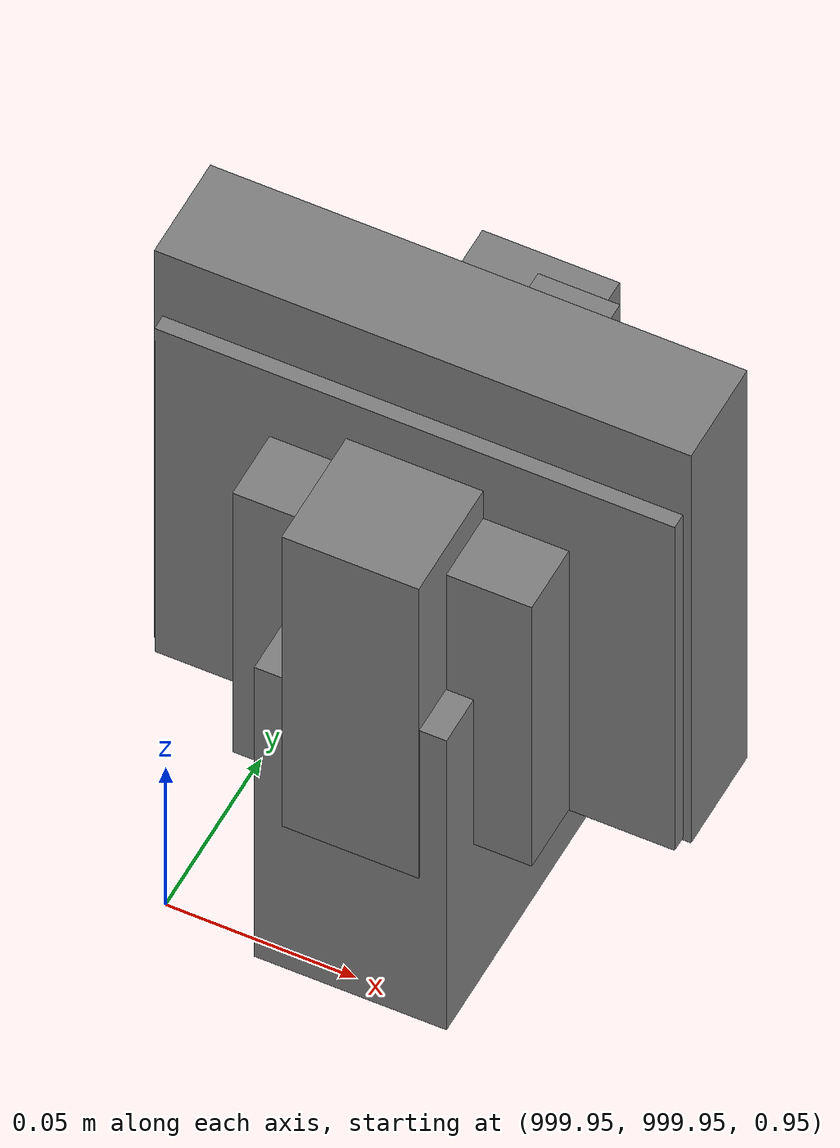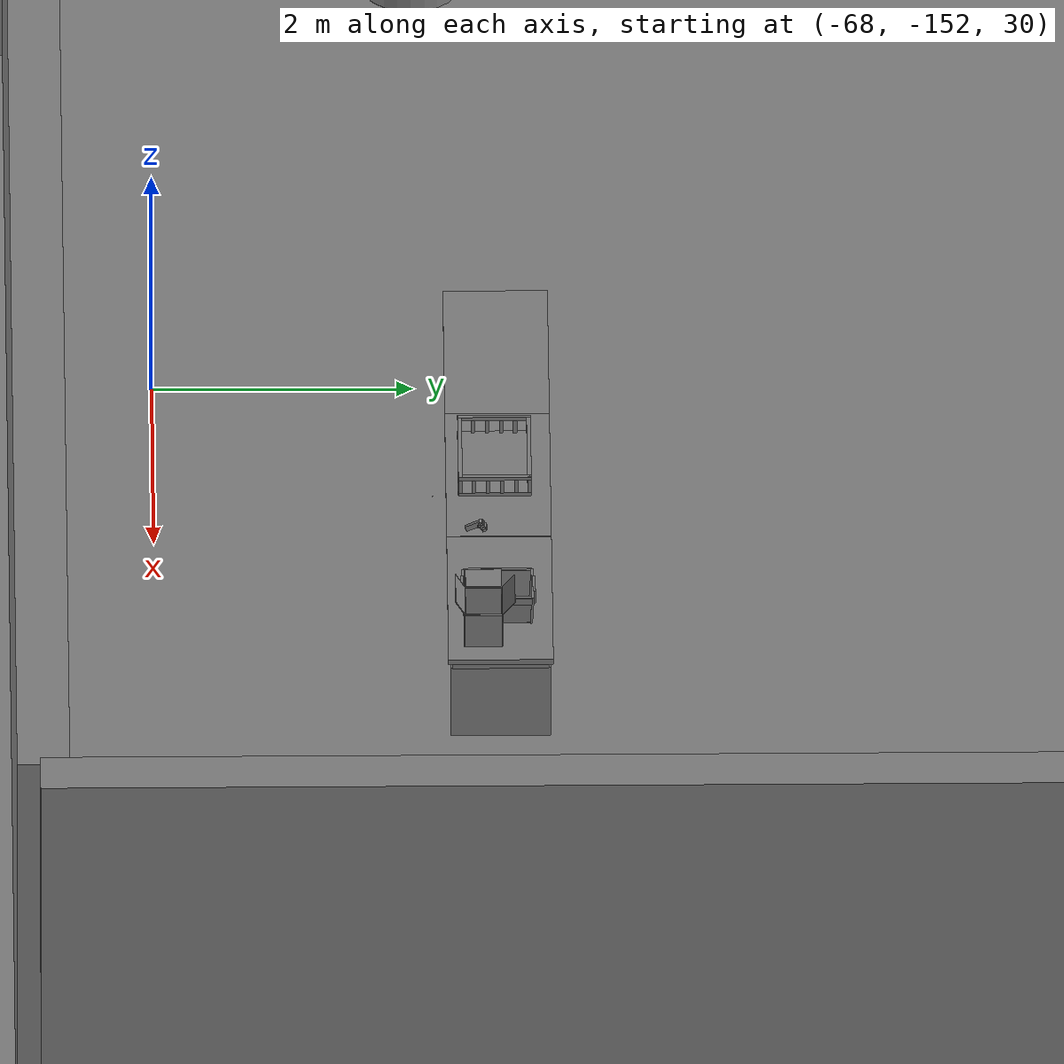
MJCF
<mujoco>
    <option gravity="0.000000000 0.000000000 -9.810000420" timestep="0.0049999999" integrator="implicitfast" density="1.225" viscosity="1.8000001e-05" noslip_iterations="10" iterations="100" sdf_iterations="50">
        <flag multiccd="disable"/>
    </option>
    <size memory="1000M"/>
    <compiler coordinate="local"/>
    <worldbody>
        <light cutoff="30" pos="0 1 1" dir="0 -1 -2"/>
        <light cutoff="30" pos="0 -1 1" dir="0 1 -2"/>
        <body pos="1000.000000000 1000.000000000 1.000000000" euler="0.000000000 0.000000000 180.000000000" name="openloong_gripper_2f85_fix_base_usda_cpu_fan">
            <geom contype="1" conaffinity="1" density="1000" type="box" material="" rgba="0.500000000 0.500000000 0.500000000 1.000000000" solimp="0.899999976 0.949999988 0.001000000" friction="1.000000000 0.005000000 0.000100000" solref="0.020000000 1.000000000" margin="0" condim="3" group="0" pos="0.000000000 0.000000000 0.070034981" quat="0.000000000 0.000000000 0.000000000 1.000000000" size="0.070700005 0.014699999 0.070700005" name="openloong_gripper_2f85_fix_base_usda_geom_51B94DEC_C32E_40E4_982D_010AF30A63FB"/>
            <freejoint name="openloong_gripper_2f85_fix_base_usda_cpu_fan_joint"/>
            <site size="0.005000000 0.005000000 0.005000000" rgba="0.500000000 0.500000000 0.500000000 1.000000000" pos="0.000000000 0.000000000 0.000000000" quat="0.999961913 0.008726535 0.000000000 0.000000000" group="0" type="sphere" name="openloong_gripper_2f85_fix_base_usda_cpu_fancsite"/>
        </body>
        <body pos="1000.000000000 1000.000000000 1.000000000" euler="0.000000000 0.000000000 180.000000000" name="openloong_gripper_2f85_fix_base_usda_wifi_box">
            <geom contype="1" conaffinity="1" density="1000" type="box" material="" rgba="0.500000000 0.500000000 0.500000000 1.000000000" solimp="0.899999976 0.949999988 0.001000000" friction="1.000000000 0.005000000 0.000100000" solref="0.020000000 1.000000000" margin="0" condim="3" group="0" pos="0.000000000 0.000000000 0.058978677" quat="0.000000000 0.000000047 0.000000000 1.000000000" size="0.068499997 0.018999999 0.059000000" name="openloong_gripper_2f85_fix_base_usda_geom_40A93B86_A2ED_4DEA_AE6B_E5F0E8280C90"/>
            <freejoint name="openloong_gripper_2f85_fix_base_usda_wifi_box_joint"/>
            <site size="0.005000000 0.005000000 0.005000000" rgba="0.500000000 0.500000000 0.500000000 1.000000000" pos="0.000000000 0.000000000 0.000000000" quat="0.999961913 0.008726500 0.000000000 0.000000000" group="0" type="sphere" name="openloong_gripper_2f85_fix_base_usda_wifi_boxsite"/>
        </body>
        <body pos="1000.000000000 1000.000000000 1.000000000" euler="0.000011953 0.000005123 -179.999984741" name="openloong_gripper_2f85_fix_base_usda_intel_box">
            <geom contype="1" conaffinity="1" density="1000" type="box" material="" rgba="0.500000000 0.500000000 0.500000000 1.000000000" solimp="0.899999976 0.949999988 0.001000000" friction="1.000000000 0.005000000 0.000100000" solref="0.020000000 1.000000000" margin="0" condim="3" group="0" pos="0.000000000 -0.000067139 0.000082284" quat="0.707106709 0.000000225 0.000000253 0.707106650" size="0.052800003 0.025300000 0.052800003" name="openloong_gripper_2f85_fix_base_usda_geom_B091ED78_F86D_430C_921C_D8D2CFFB9324"/>
            <freejoint name="openloong_gripper_2f85_fix_base_usda_intel_box_joint"/>
            <site size="0.005000000 0.005000000 0.005000000" rgba="0.500000000 0.500000000 0.500000000 1.000000000" pos="0.000000000 0.000000000 0.000000000" quat="0.999961913 0.008726500 0.000000000 0.000000000" group="0" type="sphere" name="openloong_gripper_2f85_fix_base_usda_intel_boxsite"/>
        </body>
        <body pos="-65.937934875 -149.152908325 31.166717529" euler="-17.111810684 59.860530853 -13.055556297" mocap="true" name="spotlight6_SpotLight"/>
        <body pos="1000.000000000 1000.000000000 1.000000000" euler="0.000000000 0.000000000 180.000000000" name="openloong_gripper_2f85_fix_base_usda_battery_01">
            <geom contype="1" conaffinity="1" density="1000" type="box" material="" rgba="0.500000000 0.500000000 0.500000000 1.000000000" solimp="0.899999976 0.949999988 0.001000000" friction="1.000000000 0.005000000 0.000100000" solref="0.020000000 1.000000000" margin="0" condim="3" group="0" pos="-0.011123657 -0.041940309 0.101691343" quat="1.000000000 0.000000000 0.000000000 0.000000000" size="0.010800000 0.003375000 0.004725000" name="openloong_gripper_2f85_fix_base_usda_geom_89663F50_2AE7_4988_8BDB_6B2B8C5637CB"/>
            <geom contype="1" conaffinity="1" density="1000" type="box" material="" rgba="0.500000000 0.500000000 0.500000000 1.000000000" solimp="0.899999976 0.949999988 0.001000000" friction="1.000000000 0.005000000 0.000100000" solref="0.020000000 1.000000000" margin="0" condim="3" group="0" pos="-0.010876465 -0.044247437 0.047066893" quat="0.998702705 -0.050920475 0.000000000 0.000000000" size="0.009450001 0.002700000 0.024975000" name="openloong_gripper_2f85_fix_base_usda_geom_7F7825BB_C44E_46A7_AC6F_16BA5A8D714A"/>
            <geom contype="1" conaffinity="1" density="1000" type="box" material="" rgba="0.500000000 0.500000000 0.500000000 1.000000000" solimp="0.899999976 0.949999988 0.001000000" friction="1.000000000 0.005000000 0.000100000" solref="0.020000000 1.000000000" margin="0" condim="3" group="0" pos="-0.001235962 -0.000659180 0.047381196" quat="1.000000000 0.000000000 0.000000000 0.000000000" size="0.039420001 0.039150000 0.047250003" name="openloong_gripper_2f85_fix_base_usda_geom_22B7E8DC_71FF_4CB2_85C9_D2CB68DF3EF8"/>
            <geom contype="1" conaffinity="1" density="1000" type="box" material="" rgba="0.500000000 0.500000000 0.500000000 1.000000000" solimp="0.899999976 0.949999988 0.001000000" friction="1.000000000 0.005000000 0.000100000" solref="0.020000000 1.000000000" margin="0" condim="3" group="0" pos="-0.010876465 -0.039138794 0.009851727" quat="1.000000000 0.000000000 0.000000000 0.000000000" size="0.009450001 0.010800000 0.013500000" name="openloong_gripper_2f85_fix_base_usda_geom_6B9BD9CD_B28F_40BD_B7D0_EAB54149AAB2"/>
            <geom contype="1" conaffinity="1" density="1000" type="box" material="" rgba="0.500000000 0.500000000 0.500000000 1.000000000" solimp="0.899999976 0.949999988 0.001000000" friction="1.000000000 0.005000000 0.000100000" solref="0.020000000 1.000000000" margin="0" condim="3" group="0" pos="-0.010876465 -0.041528322 0.071508206" quat="1.000000000 0.000000000 0.000000000 0.000000000" size="0.009450001 0.002700000 0.027000001" name="openloong_gripper_2f85_fix_base_usda_geom_7239FC3A_671F_4F9D_957B_E3C56A9259FC"/>
            <freejoint name="openloong_gripper_2f85_fix_base_usda_battery_01_joint"/>
            <site size="0.005000000 0.005000000 0.005000000" rgba="0.500000000 0.500000000 0.500000000 1.000000000" pos="0.000000000 0.000000000 0.000000000" quat="0.999961913 0.008726500 0.000000000 0.000000000" group="0" type="sphere" name="openloong_gripper_2f85_fix_base_usda_battery_01site"/>
        </body>
        <body pos="1000.000000000 999.999938965 1.000000000" euler="0.000000000 0.000000000 180.000000000" name="openloong_gripper_2f85_fix_base_usda_intelcore_i5">
            <geom contype="1" conaffinity="1" density="1000" type="box" material="" rgba="0.500000000 0.500000000 0.500000000 1.000000000" solimp="0.899999976 0.949999988 0.001000000" friction="1.000000000 0.005000000 0.000100000" solref="0.020000000 1.000000000" margin="0" condim="3" group="0" pos="0.000000000 0.000000000 0.051722717" quat="0.707106709 0.000000000 0.000000000 -0.707106769" size="0.052800000 0.018080002 0.052800000" name="openloong_gripper_2f85_fix_base_usda_geom_CD4A4704_696E_4ABF_84F1_E7E9C026DFE3"/>
            <freejoint name="openloong_gripper_2f85_fix_base_usda_intelcore_i5_joint"/>
            <site size="0.005000000 0.005000000 0.005000000" rgba="0.500000000 0.500000000 0.500000000 1.000000000" pos="0.000000000 0.000000000 0.000000000" quat="0.999961913 0.008726534 0.000000000 0.000000000" group="0" type="sphere" name="openloong_gripper_2f85_fix_base_usda_intelcore_i5site"/>
        </body>
        <body pos="-66.367630005 -148.978302002 31.163276672" euler="3.731383324 -19.897441864 137.541229248" mocap="true" name="spotlight1_SpotLight"/>
        <body pos="-66.380020142 -149.406448364 31.168989182" euler="169.078369141 -59.221385956 -120.518066406" mocap="true" name="spotlight4_SpotLight"/>
        <body pos="-64.866622925 -149.383972168 30.183746338" euler="89.999984741 89.999946594 0.000000000" name="openloong_gripper_2f85_fix_base_usda_bluebox_01">
            <geom contype="1" conaffinity="1" density="1000" type="box" material="" rgba="0.500000000 0.500000000 0.500000000 1.000000000" solimp="0.899999976 0.949999988 0.001000000" friction="1.000000000 0.005000000 0.000100000" solref="0.020000000 1.000000000" margin="0" condim="3" group="0" pos="0.276580811 0.187225342 0.000068665" quat="0.707106948 0.000077471 0.707106352 0.000077486" size="0.100000001 0.057999998 0.010000000" name="openloong_gripper_2f85_fix_base_usda_geom_8C6FF377_CFB5_4A30_BD7D_53E6BE546470"/>
            <geom contype="1" conaffinity="1" density="1000" type="box" material="" rgba="0.500000000 0.500000000 0.500000000 1.000000000" solimp="0.899999976 0.949999988 0.001000000" friction="1.000000000 0.005000000 0.000100000" solref="0.020000000 1.000000000" margin="0" condim="3" group="0" pos="0.000000000 0.002883911 0.000000000" quat="0.999999881 0.000000000 0.000000000 0.000000000" size="0.254000008 0.003000000 0.172000006" name="openloong_gripper_2f85_fix_base_usda_geom_A508AF9B_9962_47D5_8F0C_4CC554897077"/>
            <geom contype="1" conaffinity="1" density="1000" type="box" material="" rgba="0.500000000 0.500000000 0.500000000 1.000000000" solimp="0.899999976 0.949999988 0.001000000" friction="1.000000000 0.005000000 0.000100000" solref="0.020000000 1.000000000" margin="0" condim="3" group="0" pos="0.000000000 0.124874115 0.173484802" quat="0.999796331 0.020176515 -0.000000015 0.000000030" size="0.259999990 0.119999997 0.007000000" name="openloong_gripper_2f85_fix_base_usda_geom_B46E993C_518C_4572_92CF_DF9BFD6EA490"/>
            <geom contype="1" conaffinity="1" density="1000" type="box" material="" rgba="0.500000000 0.500000000 0.500000000 1.000000000" solimp="0.899999976 0.949999988 0.001000000" friction="1.000000000 0.005000000 0.000100000" solref="0.020000000 1.000000000" margin="0" condim="3" group="0" pos="0.000000000 0.124874115 -0.173469543" quat="0.999796331 -0.020176545 -0.000000015 0.000000000" size="0.259999990 0.119999997 0.007000000" name="openloong_gripper_2f85_fix_base_usda_geom_486CFFBD_3E5F_4FBD_BC25_060239129338"/>
            <geom contype="1" conaffinity="1" density="1000" type="box" material="" rgba="0.500000000 0.500000000 0.500000000 1.000000000" solimp="0.899999976 0.949999988 0.001000000" friction="1.000000000 0.005000000 0.000100000" solref="0.020000000 1.000000000" margin="0" condim="3" group="0" pos="0.000000000 0.214008331 0.188980103" quat="0.999912977 0.013176724 0.000000015 0.000000000" size="0.259999990 0.029999999 0.012500000" name="openloong_gripper_2f85_fix_base_usda_geom_D3D8DDA7_1E8D_488C_B4A3_5915FB6E0CBE"/>
            <geom contype="1" conaffinity="1" density="1000" type="box" material="" rgba="0.500000000 0.500000000 0.500000000 1.000000000" solimp="0.899999976 0.949999988 0.001000000" friction="1.000000000 0.005000000 0.000100000" solref="0.020000000 1.000000000" margin="0" condim="3" group="0" pos="-0.258361816 0.125289917 0.001876831" quat="0.702796936 -0.020792112 0.710783124 0.020769298" size="0.189999998 0.119999997 0.009000000" name="openloong_gripper_2f85_fix_base_usda_geom_4A2F142B_81DF_4A78_91CA_A8FA31103632"/>
            <geom contype="1" conaffinity="1" density="1000" type="box" material="" rgba="0.500000000 0.500000000 0.500000000 1.000000000" solimp="0.899999976 0.949999988 0.001000000" friction="1.000000000 0.005000000 0.000100000" solref="0.020000000 1.000000000" margin="0" condim="3" group="0" pos="0.000000000 0.214008331 -0.188980103" quat="0.999912977 -0.013176769 0.000000030 0.000000015" size="0.259999990 0.029999999 0.012500000" name="openloong_gripper_2f85_fix_base_usda_geom_062BBDA4_8614_42CD_AAFB_D1A666D09D98"/>
            <geom contype="1" conaffinity="1" density="1000" type="box" material="" rgba="0.500000000 0.500000000 0.500000000 1.000000000" solimp="0.899999976 0.949999988 0.001000000" friction="1.000000000 0.005000000 0.000100000" solref="0.020000000 1.000000000" margin="0" condim="3" group="0" pos="-0.276611328 0.187225342 0.000068665" quat="0.707106650 0.000077441 0.707106709 0.000077456" size="0.100000001 0.057999998 0.010000000" name="openloong_gripper_2f85_fix_base_usda_geom_867F7415_8165_4EA4_A434_D3BE07E22EFF"/>
            <geom contype="1" conaffinity="1" density="1000" type="box" material="" rgba="0.500000000 0.500000000 0.500000000 1.000000000" solimp="0.899999976 0.949999988 0.001000000" friction="1.000000000 0.005000000 0.000100000" solref="0.020000000 1.000000000" margin="0" condim="3" group="0" pos="0.258331299 0.125289917 0.001876831" quat="0.702851415 0.018856421 0.710823774 -0.019329369" size="0.189999998 0.119999997 0.009000000" name="openloong_gripper_2f85_fix_base_usda_geom_174A3C89_6F73_4BF8_A079_DB2265803376"/>
            <freejoint name="openloong_gripper_2f85_fix_base_usda_bluebox_01_joint"/>
            <site size="0.005000000 0.005000000 0.005000000" rgba="0.500000000 0.500000000 0.500000000 1.000000000" pos="0.000000000 0.000000000 0.000000000" quat="0.999961913 0.008726534 0.000000000 0.000000000" group="0" type="sphere" name="openloong_gripper_2f85_fix_base_usda_bluebox_01site"/>
        </body>
        <body pos="-64.496299744 -149.491867065 30.235729218" euler="0.000000000 0.000000000 89.999946594" name="openloong_gripper_2f85_fix_base_usda_cardboardbox_01">
            <geom contype="1" conaffinity="1" density="1000" type="box" material="" rgba="0.500000000 0.500000000 0.500000000 1.000000000" solimp="0.899999976 0.949999988 0.001000000" friction="1.000000000 0.005000000 0.000100000" solref="0.020000000 1.000000000" margin="0" condim="3" group="0" pos="-0.003166199 -0.004086494 0.005052090" quat="1.000000000 0.000000000 0.000000000 0.000000000" size="0.142499998 0.177500010 0.005000000" name="openloong_gripper_2f85_fix_base_usda_geom_4CA328BB_9B69_4A48_B39A_E90315986EB4"/>
            <geom contype="1" conaffinity="1" density="1000" type="box" material="" rgba="0.500000000 0.500000000 0.500000000 1.000000000" solimp="0.899999976 0.949999988 0.001000000" friction="1.000000000 0.005000000 0.000100000" solref="0.020000000 1.000000000" margin="0" condim="3" group="0" pos="-0.003166199 0.170316696 0.150570869" quat="1.000000000 0.000000000 0.000000000 0.000000000" size="0.142499998 0.005000000 0.149999991" name="openloong_gripper_2f85_fix_base_usda_geom_07A81280_EAC2_49C7_9AAE_E0165D18A780"/>
            <geom contype="1" conaffinity="1" density="1000" type="box" material="" rgba="0.500000000 0.500000000 0.500000000 1.000000000" solimp="0.899999976 0.949999988 0.001000000" friction="1.000000000 0.005000000 0.000100000" solref="0.020000000 1.000000000" margin="0" condim="3" group="0" pos="-0.147399902 -0.005307198 0.150570869" quat="1.000000000 0.000000000 0.000000000 0.000000000" size="0.005000000 0.177500010 0.149999991" name="openloong_gripper_2f85_fix_base_usda_geom_0E61C18C_7CA9_4F7B_8781_61186A26ADC7"/>
            <geom contype="1" conaffinity="1" density="1000" type="box" material="" rgba="0.500000000 0.500000000 0.500000000 1.000000000" solimp="0.899999976 0.949999988 0.001000000" friction="1.000000000 0.005000000 0.000100000" solref="0.020000000 1.000000000" margin="0" condim="3" group="0" pos="0.140275955 -0.005307198 0.150570869" quat="1.000000000 0.000000000 0.000000000 0.000000000" size="0.005000000 0.177500010 0.149999991" name="openloong_gripper_2f85_fix_base_usda_geom_05CC8B3A_A063_42CB_8AA5_0E502469866C"/>
            <geom contype="1" conaffinity="1" density="1000" type="box" material="" rgba="0.500000000 0.500000000 0.500000000 1.000000000" solimp="0.899999976 0.949999988 0.001000000" friction="1.000000000 0.005000000 0.000100000" solref="0.020000000 1.000000000" margin="0" condim="3" group="0" pos="-0.003166199 -0.181550980 0.150570869" quat="1.000000000 0.000000000 0.000000000 0.000000000" size="0.142499998 0.005000000 0.149999991" name="openloong_gripper_2f85_fix_base_usda_geom_0D530D4F_301B_4413_A29F_95DB0F2FA8A7"/>
            <freejoint name="openloong_gripper_2f85_fix_base_usda_cardboardbox_01_joint"/>
            <site size="0.005000000 0.005000000 0.005000000" rgba="0.500000000 0.500000000 0.500000000 1.000000000" pos="0.000000000 0.000000000 0.000000000" quat="0.999961913 0.008726535 0.000000000 0.000000000" group="0" type="sphere" name="openloong_gripper_2f85_fix_base_usda_site_2D18CF46_E817_463E_B7E8_7C4DBB14EAEF"/>
            <body pos="0.139160156 -0.004048347 0.301930904" euler="-179.999954224 49.383502960 179.999954224" name="openloong_gripper_2f85_fix_base_usda_A1_006">
                <geom contype="1" conaffinity="1" density="1000" type="box" material="" rgba="0.500000000 0.500000000 0.500000000 1.000000000" solimp="0.899999976 0.949999988 0.001000000" friction="1.000000000 0.005000000 0.000100000" solref="0.020000000 1.000000000" margin="0" condim="3" group="0" pos="-0.071587563 0.000009537 0.001745224" quat="0.999999881 0.000000000 0.000000000 0.000000000" size="0.071249999 0.179999992 0.002500000" name="openloong_gripper_2f85_fix_base_usda_geom_4AD0F250_0B86_43E2_95EF_7F52E818FFED"/>
                <joint armature="0" stiffness="0.07" damping="0.0099999998" axis="0.000000 1.000000 0.000000" type="hinge" name="openloong_gripper_2f85_fix_base_usda_A1_006"/>
            </body>
            <body pos="-0.145902634 -0.004086494 0.301938057" euler="-180.000000000 -60.000011444 -180.000000000" name="openloong_gripper_2f85_fix_base_usda_A2_006">
                <geom contype="1" conaffinity="1" density="1000" type="box" material="" rgba="0.500000000 0.500000000 0.500000000 1.000000000" solimp="0.899999976 0.949999988 0.001000000" friction="1.000000000 0.005000000 0.000100000" solref="0.020000000 1.000000000" margin="0" condim="3" group="0" pos="0.071268082 0.000009537 0.002717972" quat="0.000002921 0.000000000 -0.000000030 0.999999881" size="0.071249999 0.179999992 0.002500000" name="openloong_gripper_2f85_fix_base_usda_geom_CBC72064_A8D1_4B62_905D_574DD581BF58"/>
                <joint armature="0" stiffness="0.07" damping="0.0099999998" axis="0.000000 1.000000 0.000000" type="hinge" name="openloong_gripper_2f85_fix_base_usda_A2_006"/>
            </body>
            <body pos="-0.003385544 0.175991058 0.301930904" euler="-125.858116150 -0.000004561 0.000002331" name="openloong_gripper_2f85_fix_base_usda_B2_006">
                <geom contype="1" conaffinity="1" density="1000" type="box" material="" rgba="0.500000000 0.500000000 0.500000000 1.000000000" solimp="0.899999976 0.949999988 0.001000000" friction="1.000000000 0.005000000 0.000100000" solref="0.020000000 1.000000000" margin="0" condim="3" group="0" pos="0.000009537 -0.070939064 -0.002470016" quat="0.999614120 0.027776197 -0.000000015 0.000000030" size="0.137500003 0.064999998 0.005000000" name="openloong_gripper_2f85_fix_base_usda_geom_CA64BBE6_ED1A_4C60_8FCE_97A433F8F04A"/>
                <joint armature="0" stiffness="0.07" damping="0.0099999998" axis="1.000000 0.000000 0.000000" type="hinge" name="openloong_gripper_2f85_fix_base_usda_B2_006"/>
            </body>
            <body pos="-0.003385544 -0.184140205 0.301938057" euler="147.805557251 0.000000000 0.000000000" name="openloong_gripper_2f85_fix_base_usda_B1_006">
                <geom contype="1" conaffinity="1" density="1000" type="box" material="" rgba="0.500000000 0.500000000 0.500000000 1.000000000" solimp="0.899999976 0.949999988 0.001000000" friction="1.000000000 0.005000000 0.000100000" solref="0.020000000 1.000000000" margin="0" condim="3" group="0" pos="-0.000028610 0.070202351 -0.002703667" quat="0.999614179 -0.027776167 0.000000000 0.000000000" size="0.137500003 0.064999998 0.005000000" name="openloong_gripper_2f85_fix_base_usda_geom_C0CE4077_CBCA_4590_BE81_1EA43CE67248"/>
                <joint armature="0" stiffness="0.07" damping="0.0099999998" axis="1.000000 0.000000 0.000000" type="hinge" name="openloong_gripper_2f85_fix_base_usda_B1_006"/>
            </body>
        </body>
        <body pos="-65.882858276 -149.481979370 30.229999542" euler="-64.487716675 0.000000000 0.000000000" name="openloong_gripper_2f85_fix_base_usda_Barcode">
            <geom contype="1" conaffinity="1" density="1000" type="box" material="" rgba="0.500000000 0.500000000 0.500000000 1.000000000" solimp="0.899999976 0.949999988 0.001000000" friction="1.000000000 0.005000000 0.000100000" solref="0.020000000 1.000000000" margin="0" condim="3" group="0" pos="0.000000000 0.013038635 0.001419067" quat="0.000000000 0.000000000 0.000000000 1.000000119" size="0.034000002 0.010000000 0.017999999" name="openloong_gripper_2f85_fix_base_usda_geom_501C8275_6B13_41ED_8DAC_1B305400C83F"/>
            <geom contype="1" conaffinity="1" density="1000" type="box" material="" rgba="0.500000000 0.500000000 0.500000000 1.000000000" solimp="0.899999976 0.949999988 0.001000000" friction="1.000000000 0.005000000 0.000100000" solref="0.020000000 1.000000000" margin="0" condim="3" group="0" pos="0.000000000 -0.035301208 -0.007095337" quat="0.000000000 0.000000000 -0.043619365 0.999048233" size="0.028999999 0.010000000 0.020000000" name="openloong_gripper_2f85_fix_base_usda_geom_35415214_BCF3_48D3_953C_2BE7B0C4C178"/>
            <geom contype="1" conaffinity="1" density="1000" type="box" material="" rgba="0.500000000 0.500000000 0.500000000 1.000000000" solimp="0.899999976 0.949999988 0.001000000" friction="1.000000000 0.005000000 0.000100000" solref="0.020000000 1.000000000" margin="0" condim="3" group="0" pos="0.000000000 -0.043411255 -0.011749268" quat="0.922262907 0.386563420 0.000000000 0.000000000" size="0.026000001 0.010000000 0.020000000" name="openloong_gripper_2f85_fix_base_usda_geom_D2631BFB_5065_41D3_94B3_8792D86E278E"/>
            <geom contype="1" conaffinity="1" density="1000" type="box" material="" rgba="0.500000000 0.500000000 0.500000000 1.000000000" solimp="0.899999976 0.949999988 0.001000000" friction="1.000000000 0.005000000 0.000100000" solref="0.020000000 1.000000000" margin="0" condim="3" group="0" pos="0.000000000 -0.016967773 -0.031860352" quat="0.000000000 0.000000000 0.000000000 1.000000119" size="0.008000000 0.010000000 0.013000000" name="openloong_gripper_2f85_fix_base_usda_geom_4D64F68B_3B2E_4762_A044_01E131DA5CB5"/>
            <geom contype="1" conaffinity="1" density="1000" type="box" material="" rgba="0.500000000 0.500000000 0.500000000 1.000000000" solimp="0.899999976 0.949999988 0.001000000" friction="1.000000000 0.005000000 0.000100000" solref="0.020000000 1.000000000" margin="0" condim="3" group="0" pos="0.000000000 -0.001869202 0.000312805" quat="0.953716993 0.300705761 0.000000000 0.000000000" size="0.032000002 0.010000000 0.018999999" name="openloong_gripper_2f85_fix_base_usda_geom_75AC7932_BB3A_428B_8AD6_2FFDFA6CDE3E"/>
            <geom contype="1" conaffinity="1" density="1000" type="box" material="" rgba="0.500000000 0.500000000 0.500000000 1.000000000" solimp="0.899999976 0.949999988 0.001000000" friction="1.000000000 0.005000000 0.000100000" solref="0.020000000 1.000000000" margin="0" condim="3" group="0" pos="0.000000000 -0.019531250 -0.003173828" quat="0.953716993 0.300705761 0.000000000 0.000000000" size="0.030999999 0.010000000 0.020000000" name="openloong_gripper_2f85_fix_base_usda_geom_6708EC07_5D48_432B_9346_4FAC664886CA"/>
            <geom contype="1" conaffinity="1" density="1000" type="box" material="" rgba="0.500000000 0.500000000 0.500000000 1.000000000" solimp="0.899999976 0.949999988 0.001000000" friction="1.000000000 0.005000000 0.000100000" solref="0.020000000 1.000000000" margin="0" condim="3" group="0" pos="0.000000000 -0.035301208 -0.007095337" quat="0.953716993 0.300705761 0.000000000 0.000000000" size="0.028999999 0.010000000 0.020000000" name="openloong_gripper_2f85_fix_base_usda_geom_C4726BE8_6AE4_4C8E_8578_77DB58C35D5D"/>
            <geom contype="1" conaffinity="1" density="1000" type="box" material="" rgba="0.500000000 0.500000000 0.500000000 1.000000000" solimp="0.899999976 0.949999988 0.001000000" friction="1.000000000 0.005000000 0.000100000" solref="0.020000000 1.000000000" margin="0" condim="3" group="0" pos="0.000000000 -0.042617798 -0.071121216" quat="0.000000000 0.000000000 0.000000000 1.000000119" size="0.013000000 0.021000000 0.059999999" name="openloong_gripper_2f85_fix_base_usda_geom_CD48C86C_E11F_40F6_93E3_8CCCEF2DA986"/>
            <freejoint name="openloong_gripper_2f85_fix_base_usda_Barcode_joint"/>
            <site size="0.005000000 0.005000000 0.005000000" rgba="0.500000000 0.500000000 0.500000000 1.000000000" pos="0.000000000 0.000000000 0.000000000" quat="1.000000000 0.000000000 0.000000000 0.000000000" group="0" type="sphere" name="openloong_gripper_2f85_fix_base_usda_Barcode_site"/>
        </body>
        <body pos="-66.745018005 -149.392349243 30.184000015" euler="0.000000000 0.000000000 89.999946594" name="[22330952701026]_Basket_01">
            <geom contype="1" conaffinity="1" density="1000" type="box" material="" rgba="0.500000000 0.500000000 0.500000000 1.000000000" solimp="0.899999976 0.949999988 0.001000000" friction="1.000000000 0.005000000 0.000100000" solref="0.020000000 1.000000000" margin="0" condim="3" group="0" pos="-0.052425385 0.389207840 0.089787483" quat="0.707107008 0.000000000 0.000000000 0.707106411" size="0.014249999 0.014249999 0.059999999" name="[22330952701026]_geom_300C4941_1933_4C6B_A6D4_64D329BD8253"/>
            <geom contype="1" conaffinity="1" density="1000" type="box" material="" rgba="0.500000000 0.500000000 0.500000000 1.000000000" solimp="0.899999976 0.949999988 0.001000000" friction="1.000000000 0.005000000 0.000100000" solref="0.020000000 1.000000000" margin="0" condim="3" group="0" pos="0.264015198 -0.133043289 0.089787483" quat="0.707107008 0.000000000 0.000000000 0.707106411" size="0.014249999 0.014249999 0.059999999" name="[22330952701026]_geom_B7276703_E399_4BD0_850E_E7B3CC26DADB"/>
            <geom contype="1" conaffinity="1" density="1000" type="box" material="" rgba="0.500000000 0.500000000 0.500000000 1.000000000" solimp="0.899999976 0.949999988 0.001000000" friction="1.000000000 0.005000000 0.000100000" solref="0.020000000 1.000000000" margin="0" condim="3" group="0" pos="-0.264015198 -0.265548706 0.089793205" quat="0.707107008 0.000000000 0.000000000 0.707106411" size="0.014249999 0.014249999 0.059999999" name="[22330952701026]_geom_16FEF8D7_96FC_4B90_80B8_085931BD7AF3"/>
            <geom contype="1" conaffinity="1" density="1000" type="box" material="" rgba="0.500000000 0.500000000 0.500000000 1.000000000" solimp="0.899999976 0.949999988 0.001000000" friction="1.000000000 0.005000000 0.000100000" solref="0.020000000 1.000000000" margin="0" condim="3" group="0" pos="-0.160263062 -0.389322281 0.089793205" quat="0.707107008 0.000000000 0.000000000 0.707106411" size="0.014249999 0.014249999 0.059999999" name="[22330952701026]_geom_E4C44F40_3260_4E8B_BBF5_2FA6B862D73E"/>
            <geom contype="1" conaffinity="1" density="1000" type="box" material="" rgba="0.500000000 0.500000000 0.500000000 1.000000000" solimp="0.899999976 0.949999988 0.001000000" friction="1.000000000 0.005000000 0.000100000" solref="0.020000000 1.000000000" margin="0" condim="3" group="0" pos="0.162265778 -0.389322281 0.089787483" quat="0.707107008 0.000000000 0.000000000 0.707106411" size="0.014249999 0.014249999 0.059999999" name="[22330952701026]_geom_598C310B_9666_42EF_8110_136B7CFA7C84"/>
            <geom contype="1" conaffinity="1" density="1000" type="box" material="" rgba="0.500000000 0.500000000 0.500000000 1.000000000" solimp="0.899999976 0.949999988 0.001000000" friction="1.000000000 0.005000000 0.000100000" solref="0.020000000 1.000000000" margin="0" condim="3" group="0" pos="0.264015198 0.389207840 0.089787483" quat="0.707107008 0.000000000 0.000000000 0.707106411" size="0.014249999 0.014249999 0.059999999" name="[22330952701026]_geom_1FA0A4F2_8AD9_43CA_A431_3D669B615D70"/>
            <geom contype="1" conaffinity="1" density="1000" type="box" material="" rgba="0.500000000 0.500000000 0.500000000 1.000000000" solimp="0.899999976 0.949999988 0.001000000" friction="1.000000000 0.005000000 0.000100000" solref="0.020000000 1.000000000" margin="0" condim="3" group="0" pos="-0.264015198 -0.133043289 0.089793205" quat="0.707107008 0.000000000 0.000000000 0.707106411" size="0.014249999 0.014249999 0.059999999" name="[22330952701026]_geom_F3D286ED_411B_4D1E_9593_558F9C3C388E"/>
            <geom contype="1" conaffinity="1" density="1000" type="box" material="" rgba="0.500000000 0.500000000 0.500000000 1.000000000" solimp="0.899999976 0.949999988 0.001000000" friction="1.000000000 0.005000000 0.000100000" solref="0.020000000 1.000000000" margin="0" condim="3" group="0" pos="-0.264026642 0.269256592 0.089793205" quat="0.707107008 0.000000000 0.000000000 0.707106411" size="0.014249999 0.014249999 0.059999999" name="[22330952701026]_geom_5BA5255F_7DB5_4D78_964E_3BD75DA051D1"/>
            <geom contype="1" conaffinity="1" density="1000" type="box" material="" rgba="0.500000000 0.500000000 0.500000000 1.000000000" solimp="0.899999976 0.949999988 0.001000000" friction="1.000000000 0.005000000 0.000100000" solref="0.020000000 1.000000000" margin="0" condim="3" group="0" pos="0.054462433 0.389207840 0.089787483" quat="0.707107008 0.000000000 0.000000000 0.707106411" size="0.014249999 0.014249999 0.059999999" name="[22330952701026]_geom_1C94C4E6_5B08_4302_81E3_44138A38F80F"/>
            <geom contype="1" conaffinity="1" density="1000" type="box" material="" rgba="0.500000000 0.500000000 0.500000000 1.000000000" solimp="0.899999976 0.949999988 0.001000000" friction="1.000000000 0.005000000 0.000100000" solref="0.020000000 1.000000000" margin="0" condim="3" group="0" pos="0.054462433 -0.389322281 0.089787483" quat="0.707107008 0.000000000 0.000000000 0.707106411" size="0.014249999 0.014249999 0.059999999" name="[22330952701026]_geom_02BB5710_7016_4C73_8465_A33A5926509D"/>
            <geom contype="1" conaffinity="1" density="1000" type="box" material="" rgba="0.500000000 0.500000000 0.500000000 1.000000000" solimp="0.899999976 0.949999988 0.001000000" friction="1.000000000 0.005000000 0.000100000" solref="0.020000000 1.000000000" margin="0" condim="3" group="0" pos="0.264015198 0.269256592 0.089793205" quat="0.707107008 0.000000000 0.000000000 0.707106411" size="0.014249999 0.014249999 0.059999999" name="[22330952701026]_geom_3AEF5575_F00B_48E3_9C1A_0E20F60AF826"/>
            <geom contype="1" conaffinity="1" density="1000" type="box" material="" rgba="0.500000000 0.500000000 0.500000000 1.000000000" solimp="0.899999976 0.949999988 0.001000000" friction="1.000000000 0.005000000 0.000100000" solref="0.020000000 1.000000000" margin="0" condim="3" group="0" pos="0.264015198 -0.389322281 0.089787483" quat="0.707107008 0.000000000 0.000000000 0.707106411" size="0.014249999 0.014249999 0.059999999" name="[22330952701026]_geom_DD8835A5_F081_416E_A730_091B77B241A3"/>
            <geom contype="1" conaffinity="1" density="1000" type="box" material="" rgba="0.500000000 0.500000000 0.500000000 1.000000000" solimp="0.899999976 0.949999988 0.001000000" friction="1.000000000 0.005000000 0.000100000" solref="0.020000000 1.000000000" margin="0" condim="3" group="0" pos="0.000000000 0.000000000 0.015998840" quat="0.707107008 0.000000000 0.000000000 0.707106411" size="0.403499991 0.279000014 0.015750000" name="[22330952701026]_geom_BF8483F1_2427_4904_91AE_B877EEF23D8D"/>
            <geom contype="1" conaffinity="1" density="1000" type="box" material="" rgba="0.500000000 0.500000000 0.500000000 1.000000000" solimp="0.899999976 0.949999988 0.001000000" friction="1.000000000 0.005000000 0.000100000" solref="0.020000000 1.000000000" margin="0" condim="3" group="0" pos="0.000000000 -0.389476776 0.163619041" quat="0.707107008 0.000000000 0.000000000 0.707106411" size="0.015000000 0.277500004 0.015750000" name="[22330952701026]_geom_FC401D77_9281_48E5_A11A_AAA8B5FEF03B"/>
            <geom contype="1" conaffinity="1" density="1000" type="box" material="" rgba="0.500000000 0.500000000 0.500000000 1.000000000" solimp="0.899999976 0.949999988 0.001000000" friction="1.000000000 0.005000000 0.000100000" solref="0.020000000 1.000000000" margin="0" condim="3" group="0" pos="0.162265778 0.389207840 0.089787483" quat="0.707107008 0.000000000 0.000000000 0.707106411" size="0.014249999 0.014249999 0.059999999" name="[22330952701026]_geom_2B375F92_DA58_4D17_84AF_4FB140C22C56"/>
            <geom contype="1" conaffinity="1" density="1000" type="box" material="" rgba="0.500000000 0.500000000 0.500000000 1.000000000" solimp="0.899999976 0.949999988 0.001000000" friction="1.000000000 0.005000000 0.000100000" solref="0.020000000 1.000000000" margin="0" condim="3" group="0" pos="0.000000000 0.389471054 0.163619041" quat="0.707107008 0.000000000 0.000000000 0.707106411" size="0.015000000 0.277500004 0.015750000" name="[22330952701026]_geom_72AA2E56_A0A6_4D14_BFD7_D4840C140727"/>
            <geom contype="1" conaffinity="1" density="1000" type="box" material="" rgba="0.500000000 0.500000000 0.500000000 1.000000000" solimp="0.899999976 0.949999988 0.001000000" friction="1.000000000 0.005000000 0.000100000" solref="0.020000000 1.000000000" margin="0" condim="3" group="0" pos="-0.263511658 0.000000000 0.163619041" quat="0.707107008 0.000000000 0.000000000 0.707106411" size="0.403499991 0.015000000 0.015750000" name="[22330952701026]_geom_189E95E0_D0F5_44E5_9D22_271A383338DD"/>
            <geom contype="1" conaffinity="1" density="1000" type="box" material="" rgba="0.500000000 0.500000000 0.500000000 1.000000000" solimp="0.899999976 0.949999988 0.001000000" friction="1.000000000 0.005000000 0.000100000" solref="0.020000000 1.000000000" margin="0" condim="3" group="0" pos="-0.264015198 0.141334534 0.089793205" quat="0.707107008 0.000000000 0.000000000 0.707106411" size="0.014249999 0.014249999 0.059999999" name="[22330952701026]_geom_D264883C_6DBB_4003_A245_5B57B0A2A9D1"/>
            <geom contype="1" conaffinity="1" density="1000" type="box" material="" rgba="0.500000000 0.500000000 0.500000000 1.000000000" solimp="0.899999976 0.949999988 0.001000000" friction="1.000000000 0.005000000 0.000100000" solref="0.020000000 1.000000000" margin="0" condim="3" group="0" pos="0.264015198 -0.265548706 0.089787483" quat="0.707107008 0.000000000 0.000000000 0.707106411" size="0.014249999 0.014249999 0.059999999" name="[22330952701026]_geom_6B697893_CAF7_43CD_8B64_54445BAC125C"/>
            <geom contype="1" conaffinity="1" density="1000" type="box" material="" rgba="0.500000000 0.500000000 0.500000000 1.000000000" solimp="0.899999976 0.949999988 0.001000000" friction="1.000000000 0.005000000 0.000100000" solref="0.020000000 1.000000000" margin="0" condim="3" group="0" pos="-0.160263062 0.389207840 0.089787483" quat="0.707107008 0.000000000 0.000000000 0.707106411" size="0.014249999 0.014249999 0.059999999" name="[22330952701026]_geom_4DCA966E_08ED_4A04_8605_973CDABD54E2"/>
            <geom contype="1" conaffinity="1" density="1000" type="box" material="" rgba="0.500000000 0.500000000 0.500000000 1.000000000" solimp="0.899999976 0.949999988 0.001000000" friction="1.000000000 0.005000000 0.000100000" solref="0.020000000 1.000000000" margin="0" condim="3" group="0" pos="-0.052425385 -0.389322281 0.089787483" quat="0.707107008 0.000000000 0.000000000 0.707106411" size="0.014249999 0.014249999 0.059999999" name="[22330952701026]_geom_68CF846D_13A1_4210_A8F8_1516CEEDB226"/>
            <geom contype="1" conaffinity="1" density="1000" type="box" material="" rgba="0.500000000 0.500000000 0.500000000 1.000000000" solimp="0.899999976 0.949999988 0.001000000" friction="1.000000000 0.005000000 0.000100000" solref="0.020000000 1.000000000" margin="0" condim="3" group="0" pos="-0.264026642 -0.389322281 0.089793205" quat="0.707107008 0.000000000 0.000000000 0.707106411" size="0.014249999 0.014249999 0.059999999" name="[22330952701026]_geom_A2D716C1_1B1E_4FEE_94E7_A84671301E87"/>
            <geom contype="1" conaffinity="1" density="1000" type="box" material="" rgba="0.500000000 0.500000000 0.500000000 1.000000000" solimp="0.899999976 0.949999988 0.001000000" friction="1.000000000 0.005000000 0.000100000" solref="0.020000000 1.000000000" margin="0" condim="3" group="0" pos="0.264015198 0.141334534 0.089787483" quat="0.707107008 0.000000000 0.000000000 0.707106411" size="0.014249999 0.014249999 0.059999999" name="[22330952701026]_geom_3C548389_0A4D_421E_9FC1_4D318DDA09AB"/>
            <geom contype="1" conaffinity="1" density="1000" type="box" material="" rgba="0.500000000 0.500000000 0.500000000 1.000000000" solimp="0.899999976 0.949999988 0.001000000" friction="1.000000000 0.005000000 0.000100000" solref="0.020000000 1.000000000" margin="0" condim="3" group="0" pos="-0.264015198 0.389207840 0.089793205" quat="0.707107008 0.000000000 0.000000000 0.707106411" size="0.014249999 0.014249999 0.059999999" name="[22330952701026]_geom_5B546D0A_7169_4782_97D7_0EA073DCDAC7"/>
            <geom contype="1" conaffinity="1" density="1000" type="box" material="" rgba="0.500000000 0.500000000 0.500000000 1.000000000" solimp="0.899999976 0.949999988 0.001000000" friction="1.000000000 0.005000000 0.000100000" solref="0.020000000 1.000000000" margin="0" condim="3" group="0" pos="0.264015198 0.004480362 0.089787483" quat="0.707107008 0.000000000 0.000000000 0.707106411" size="0.014249999 0.014249999 0.059999999" name="[22330952701026]_geom_08F0EA92_1E29_45CA_A623_2EC8D9CE165A"/>
            <geom contype="1" conaffinity="1" density="1000" type="box" material="" rgba="0.500000000 0.500000000 0.500000000 1.000000000" solimp="0.899999976 0.949999988 0.001000000" friction="1.000000000 0.005000000 0.000100000" solref="0.020000000 1.000000000" margin="0" condim="3" group="0" pos="0.263694763 -0.000011444 0.163619041" quat="0.707107008 0.000000000 0.000000000 0.707106411" size="0.403499991 0.015000000 0.015750000" name="[22330952701026]_geom_5E659199_C57C_4403_8AC0_E447FF9EE408"/>
            <geom contype="1" conaffinity="1" density="1000" type="box" material="" rgba="0.500000000 0.500000000 0.500000000 1.000000000" solimp="0.899999976 0.949999988 0.001000000" friction="1.000000000 0.005000000 0.000100000" solref="0.020000000 1.000000000" margin="0" condim="3" group="0" pos="-0.264015198 0.004480362 0.089793205" quat="0.707107008 0.000000000 0.000000000 0.707106411" size="0.014249999 0.014249999 0.059999999" name="[22330952701026]_geom_687A8C79_372B_4C6D_9729_1881500CFB2E"/>
            <freejoint name="[22330952701026]_joint_D50C4591_9FDD_490E_84E2_8A26C9136292"/>
        </body>
        <body pos="0.000000000 0.000000000 0.000000000" euler="0.000000000 0.000000000 0.000000000" name="Static Objects_Static Objects">
            <geom contype="1" conaffinity="1" density="1000" type="box" material="" rgba="0.500000000 0.500000000 0.500000000 1.000000000" solimp="0.899999976 0.949999988 0.001000000" friction="1.000000000 0.005000000 0.000100000" solref="0.020000000 1.000000000" margin="0" condim="3" group="0" pos="-67.544113159 -149.365814209 29.727830887" quat="0.500000417 0.499999970 0.499999553 0.499999970" size="0.381000012 0.319999993 0.041000001" name="Static Objects_geom_1CE624DF_0F7A_4299_B6F7_C4664F480D8D"/>
            <geom contype="1" conaffinity="1" density="1000" type="box" material="" rgba="0.500000000 0.500000000 0.500000000 1.000000000" solimp="0.899999976 0.949999988 0.001000000" friction="1.000000000 0.005000000 0.000100000" solref="0.020000000 1.000000000" margin="0" condim="3" group="0" pos="-68.239501953 -149.365814209 30.086868286" quat="0.500000417 0.499999970 0.499999553 0.499999970" size="0.370999992 0.039500002 0.745000005" name="Static Objects_geom_3C16BD1C_E8EB_4D8B_BB32_3262593E450C"/>
            <geom contype="1" conaffinity="1" density="1000" type="box" material="" rgba="0.500000000 0.500000000 0.500000000 1.000000000" solimp="0.899999976 0.949999988 0.001000000" friction="1.000000000 0.005000000 0.000100000" solref="0.020000000 1.000000000" margin="0" condim="3" group="0" pos="-68.239501953 -149.365814209 30.147235870" quat="0.500000417 0.499999970 0.499999553 0.499999970" size="0.400000006 0.022000000 0.800000012" name="Static Objects_geom_FCC3D8C7_DBD4_4F6D_A2F4_99A2C1DC48CD"/>
            <geom contype="1" conaffinity="1" density="1000" type="box" material="" rgba="0.500000000 0.500000000 0.500000000 1.000000000" solimp="0.899999976 0.949999988 0.001000000" friction="1.000000000 0.005000000 0.000100000" solref="0.020000000 1.000000000" margin="0" condim="3" group="0" pos="-68.934890747 -149.365814209 29.727830887" quat="0.500000417 0.499999970 0.499999553 0.499999970" size="0.381000012 0.319999993 0.041000001" name="Static Objects_geom_1805B591_92F9_4A7B_970E_D06C7BF31CD0"/>
            <geom contype="1" conaffinity="1" density="1000" type="box" material="" rgba="0.500000000 0.500000000 0.500000000 1.000000000" solimp="0.899999976 0.949999988 0.001000000" friction="1.000000000 0.005000000 0.000100000" solref="0.020000000 1.000000000" margin="0" condim="3" group="0" pos="-68.239501953 -149.365814209 29.561563492" quat="0.500000417 0.499999970 0.499999553 0.499999970" size="0.020000000 0.022000000 0.660000026" name="Static Objects_geom_B910E5E9_D99B_46C1_B066_D28C09A4C47C"/>
            <geom contype="1" conaffinity="1" density="1000" type="box" material="" rgba="0.500000000 0.500000000 0.500000000 1.000000000" solimp="0.899999976 0.949999988 0.001000000" friction="1.000000000 0.005000000 0.000100000" solref="0.020000000 1.000000000" margin="0" condim="3" group="0" pos="-65.945671082 -149.365814209 29.727830887" quat="0.500000417 0.499999970 0.499999553 0.499999970" size="0.381000012 0.319999993 0.041000001" name="Static Objects_geom_3A406428_5894_41B8_ACCA_43EE187B0D7A"/>
            <geom contype="1" conaffinity="1" density="1000" type="box" material="" rgba="0.500000000 0.500000000 0.500000000 1.000000000" solimp="0.899999976 0.949999988 0.001000000" friction="1.000000000 0.005000000 0.000100000" solref="0.020000000 1.000000000" margin="0" condim="3" group="0" pos="-66.641059875 -149.365814209 30.086868286" quat="0.500000417 0.499999970 0.499999553 0.499999970" size="0.370999992 0.039500002 0.745000005" name="Static Objects_geom_8D7F57B8_E08D_4EA3_BAE1_E8B6AEFE70E5"/>
            <geom contype="1" conaffinity="1" density="1000" type="box" material="" rgba="0.500000000 0.500000000 0.500000000 1.000000000" solimp="0.899999976 0.949999988 0.001000000" friction="1.000000000 0.005000000 0.000100000" solref="0.020000000 1.000000000" margin="0" condim="3" group="0" pos="-66.641059875 -149.365814209 30.147235870" quat="0.500000417 0.499999970 0.499999553 0.499999970" size="0.400000006 0.022000000 0.800000012" name="Static Objects_geom_4B12F341_E51D_4909_9A62_9DC7E8E5544F"/>
            <geom contype="1" conaffinity="1" density="1000" type="box" material="" rgba="0.500000000 0.500000000 0.500000000 1.000000000" solimp="0.899999976 0.949999988 0.001000000" friction="1.000000000 0.005000000 0.000100000" solref="0.020000000 1.000000000" margin="0" condim="3" group="0" pos="-67.336448669 -149.365814209 29.727830887" quat="0.500000417 0.499999970 0.499999553 0.499999970" size="0.381000012 0.319999993 0.041000001" name="Static Objects_geom_4D73E6C4_2AFB_4377_827F_37F7129B2299"/>
            <geom contype="1" conaffinity="1" density="1000" type="box" material="" rgba="0.500000000 0.500000000 0.500000000 1.000000000" solimp="0.899999976 0.949999988 0.001000000" friction="1.000000000 0.005000000 0.000100000" solref="0.020000000 1.000000000" margin="0" condim="3" group="0" pos="-66.641059875 -149.365814209 29.561563492" quat="0.500000417 0.499999970 0.499999553 0.499999970" size="0.020000000 0.022000000 0.660000026" name="Static Objects_geom_981D0AC4_7E90_48A5_B1B6_F833164118FA"/>
            <geom contype="1" conaffinity="1" density="1000" type="box" material="" rgba="0.500000000 0.500000000 0.500000000 1.000000000" solimp="0.899999976 0.949999988 0.001000000" friction="1.000000000 0.005000000 0.000100000" solref="0.020000000 1.000000000" margin="0" condim="3" group="0" pos="-64.338577271 -149.365814209 29.727830887" quat="0.500000417 0.499999970 0.499999553 0.499999970" size="0.381000012 0.319999993 0.041000001" name="Static Objects_geom_E6029640_5B0C_4806_908A_FB9E28F6E08D"/>
            <geom contype="1" conaffinity="1" density="1000" type="box" material="" rgba="0.500000000 0.500000000 0.500000000 1.000000000" solimp="0.899999976 0.949999988 0.001000000" friction="1.000000000 0.005000000 0.000100000" solref="0.020000000 1.000000000" margin="0" condim="3" group="0" pos="-65.033966064 -149.365814209 30.086868286" quat="0.500000417 0.499999970 0.499999553 0.499999970" size="0.370999992 0.039500002 0.745000005" name="Static Objects_geom_19B89CFD_A85D_4E01_88DB_B1784CBCA552"/>
            <geom contype="1" conaffinity="1" density="1000" type="box" material="" rgba="0.500000000 0.500000000 0.500000000 1.000000000" solimp="0.899999976 0.949999988 0.001000000" friction="1.000000000 0.005000000 0.000100000" solref="0.020000000 1.000000000" margin="0" condim="3" group="0" pos="-65.033966064 -149.365814209 30.147235870" quat="0.500000417 0.499999970 0.499999553 0.499999970" size="0.400000006 0.022000000 0.800000012" name="Static Objects_geom_DD59AD28_AFC5_4465_BF34_5FA8019686B9"/>
            <geom contype="1" conaffinity="1" density="1000" type="box" material="" rgba="0.500000000 0.500000000 0.500000000 1.000000000" solimp="0.899999976 0.949999988 0.001000000" friction="1.000000000 0.005000000 0.000100000" solref="0.020000000 1.000000000" margin="0" condim="3" group="0" pos="-65.729354858 -149.365814209 29.727830887" quat="0.500000417 0.499999970 0.499999553 0.499999970" size="0.381000012 0.319999993 0.041000001" name="Static Objects_geom_0EF71A16_2CB3_41FD_AD47_2627BA0BE0EC"/>
            <geom contype="1" conaffinity="1" density="1000" type="box" material="" rgba="0.500000000 0.500000000 0.500000000 1.000000000" solimp="0.899999976 0.949999988 0.001000000" friction="1.000000000 0.005000000 0.000100000" solref="0.020000000 1.000000000" margin="0" condim="3" group="0" pos="-65.033966064 -149.365814209 29.561563492" quat="0.500000417 0.499999970 0.499999553 0.499999970" size="0.020000000 0.022000000 0.660000026" name="Static Objects_geom_7011CC39_7E76_42C0_AA77_0E640A3495DD"/>
            <geom contype="1" conaffinity="1" density="1000" type="box" material="" rgba="0.500000000 0.500000000 0.500000000 1.000000000" solimp="0.899999976 0.949999988 0.001000000" friction="1.000000000 0.005000000 0.000100000" solref="0.020000000 1.000000000" margin="0" condim="3" group="0" pos="-61.754566193 -137.853729248 33.906845093" quat="0.707107067 0.000000000 0.000000000 0.707106471" size="0.759999990 0.759999990 4.500000000" name="Static Objects_geom_BD094213_02A2_46E0_83DD_3FA0CB210CD6"/>
            <geom contype="1" conaffinity="1" density="1000" type="box" material="" rgba="0.500000000 0.500000000 0.500000000 1.000000000" solimp="0.899999976 0.949999988 0.001000000" friction="1.000000000 0.005000000 0.000100000" solref="0.020000000 1.000000000" margin="0" condim="3" group="0" pos="-57.511135101 -144.927108765 31.707921982" quat="1.000000000 0.000000000 0.000000000 0.000000000" size="0.200000003 8.000000000 2.299999952" name="Static Objects_geom_E8D3B6AA_CDFB_4CFD_897F_47E147A8E6B6"/>
            <geom contype="1" conaffinity="1" density="1000" type="box" material="" rgba="0.500000000 0.500000000 0.500000000 1.000000000" solimp="0.899999976 0.949999988 0.001000000" friction="1.000000000 0.005000000 0.000100000" solref="0.020000000 1.000000000" margin="0" condim="3" group="0" pos="-80.517646790 -157.574050903 31.688196182" quat="0.707107067 0.000000000 0.000000000 0.707106471" size="0.600000024 0.600000024 2.299999952" name="Static Objects_geom_A2F9BB27_B2B1_4ADF_A58C_1BCE42ABAB54"/>
            <geom contype="1" conaffinity="1" density="1000" type="box" material="" rgba="0.500000000 0.500000000 0.500000000 1.000000000" solimp="0.899999976 0.949999988 0.001000000" friction="1.000000000 0.005000000 0.000100000" solref="0.020000000 1.000000000" margin="0" condim="3" group="0" pos="-80.711044312 -147.414932251 31.666158676" quat="1.000000000 0.000000000 0.000000000 0.000000000" size="0.200000003 10.000000000 2.299999952" name="Static Objects_geom_B2C63E6E_2AFE_47B2_986F_066876EFE30C"/>
            <geom contype="1" conaffinity="1" density="1000" type="box" material="" rgba="0.500000000 0.500000000 0.500000000 1.000000000" solimp="0.899999976 0.949999988 0.001000000" friction="1.000000000 0.005000000 0.000100000" solref="0.020000000 1.000000000" margin="0" condim="3" group="0" pos="-57.687217712 -137.434692383 31.688196182" quat="0.707107067 0.000000000 0.000000000 0.707106471" size="0.600000024 0.600000024 2.299999952" name="Static Objects_geom_A2BBAEF1_9F85_4966_98A3_C9A4D49D5F50"/>
            <geom contype="1" conaffinity="1" density="1000" type="box" material="" rgba="0.500000000 0.500000000 0.500000000 1.000000000" solimp="0.899999976 0.949999988 0.001000000" friction="1.000000000 0.005000000 0.000100000" solref="0.020000000 1.000000000" margin="0" condim="3" group="0" pos="-69.537033081 -140.263229370 31.714921951" quat="0.707107067 0.000000000 0.000000000 0.707106471" size="0.759999990 4.500000000 2.299999952" name="Static Objects_geom_008CE1FC_E55E_48C0_9922_2DC7BF7698C5"/>
            <geom contype="1" conaffinity="1" density="1000" type="box" material="" rgba="0.500000000 0.500000000 0.500000000 1.000000000" solimp="0.899999976 0.949999988 0.001000000" friction="1.000000000 0.005000000 0.000100000" solref="0.020000000 1.000000000" margin="0" condim="3" group="0" pos="-80.073638916 -137.853713989 33.906845093" quat="0.707107067 0.000000000 0.000000000 0.707106471" size="0.759999990 0.759999990 4.500000000" name="Static Objects_geom_EFD9F7F4_BF7A_4566_9331_8C4BB5B078E1"/>
            <geom contype="1" conaffinity="1" density="1000" type="box" material="" rgba="0.500000000 0.500000000 0.500000000 1.000000000" solimp="0.899999976 0.949999988 0.001000000" friction="1.000000000 0.005000000 0.000100000" solref="0.020000000 1.000000000" margin="0" condim="3" group="0" pos="-73.406707764 -155.734664917 31.707921982" quat="1.000000000 0.000000000 0.000000000 0.000000000" size="0.200000003 3.000000000 2.299999952" name="Static Objects_geom_398B0AD8_0491_47EB_9AEC_9B333F923247"/>
            <geom contype="1" conaffinity="1" density="1000" type="box" material="" rgba="0.500000000 0.500000000 0.500000000 1.000000000" solimp="0.899999976 0.949999988 0.001000000" friction="1.000000000 0.005000000 0.000100000" solref="0.020000000 1.000000000" margin="0" condim="3" group="0" pos="-68.497543335 -137.448257446 31.707921982" quat="0.707107067 0.000000000 0.000000000 0.707106471" size="0.200000003 14.000000000 2.299999952" name="Static Objects_geom_312D4B30_FAB1_4C26_A0A9_87A1749BED32"/>
            <geom contype="1" conaffinity="1" density="1000" type="cylinder" material="" rgba="0.500000000 0.500000000 0.500000000 1.000000000" solimp="0.899999976 0.949999988 0.001000000" friction="1.000000000 0.005000000 0.000100000" solref="0.020000000 1.000000000" margin="0" condim="3" group="0" pos="-68.868522644 -142.134506226 31.711090088" quat="0.707107067 0.000000000 0.000000000 0.707106471" size="0.509999990 2.299999952 1.000000000" name="Static Objects_geom_48C77DDF_3295_46DC_92FB_65C20A75A545"/>
            <geom contype="1" conaffinity="1" density="1000" type="plane" material="" rgba="0.500000000 0.500000000 0.500000000 1.000000000" solimp="0.899999976 0.949999988 0.001000000" friction="1.000000000 0.005000000 0.000100000" solref="0.020000000 1.000000000" margin="0" condim="3" group="0" pos="-72.873703003 -147.131927490 29.409669876" quat="1.000000000 0.000000000 0.000000000 0.000000000" size="18.000000000 14.000000000 1.000000000" name="Static Objects_geom_B9FC96C2_B061_4E91_A09A_1944DFFDA505"/>
            <geom contype="1" conaffinity="1" density="1000" type="box" material="" rgba="0.500000000 0.500000000 0.500000000 1.000000000" solimp="0.899999976 0.949999988 0.001000000" friction="1.000000000 0.005000000 0.000100000" solref="0.020000000 1.000000000" margin="0" condim="3" group="0" pos="-79.943580627 -157.782272339 31.707921982" quat="0.707107067 0.000000000 0.000000000 0.707106471" size="0.200000003 7.000000000 2.299999952" name="Static Objects_geom_AE112C8C_0C5E_450E_AE66_40D1E1896009"/>
            <geom contype="1" conaffinity="1" density="1000" type="box" material="" rgba="0.500000000 0.500000000 0.500000000 1.000000000" solimp="0.899999976 0.949999988 0.001000000" friction="1.000000000 0.005000000 0.000100000" solref="0.020000000 1.000000000" margin="0" condim="3" group="0" pos="-65.421028137 -152.903442383 31.707921982" quat="0.707107067 0.000000000 0.000000000 0.707106471" size="0.200000003 7.800000191 2.299999952" name="Static Objects_geom_F1071C1F_D81E_4D16_9F64_D69BD9D69E16"/>
            <geom contype="1" conaffinity="1" density="1000" type="box" material="" rgba="0.500000000 0.500000000 0.500000000 1.000000000" solimp="0.899999976 0.949999988 0.001000000" friction="1.000000000 0.005000000 0.000100000" solref="0.020000000 1.000000000" margin="0" condim="3" group="0" pos="-74.776908875 -149.964416504 31.688196182" quat="1.000000000 0.000000000 0.000000000 0.000000000" size="0.600000024 0.409999996 2.299999952" name="Static Objects_geom_812DB924_4E8A_446D_8E06_FA15DF22F597"/>
            <geom contype="1" conaffinity="1" density="1000" type="cylinder" material="" rgba="0.500000000 0.500000000 0.500000000 1.000000000" solimp="0.899999976 0.949999988 0.001000000" friction="1.000000000 0.005000000 0.000100000" solref="0.020000000 1.000000000" margin="0" condim="3" group="0" pos="-60.161884308 -142.134506226 31.711090088" quat="0.707107067 0.000000000 0.000000000 0.707106471" size="0.509999990 2.299999952 1.000000000" name="Static Objects_geom_E9924297_7A20_41FD_B854_77042A20E714"/>
            <geom contype="1" conaffinity="1" density="1000" type="cylinder" material="" rgba="0.500000000 0.500000000 0.500000000 1.000000000" solimp="0.899999976 0.949999988 0.001000000" friction="1.000000000 0.005000000 0.000100000" solref="0.020000000 1.000000000" margin="0" condim="3" group="0" pos="-75.382453918 -149.963455200 31.711090088" quat="0.707107067 0.000000000 0.000000000 0.707106471" size="0.409999996 2.299999952 1.000000000" name="Static Objects_geom_B232AEFA_030A_4224_92BD_4D641DD3A1F1"/>
            <geom contype="1" conaffinity="1" density="1000" type="cylinder" material="" rgba="0.500000000 0.500000000 0.500000000 1.000000000" solimp="0.899999976 0.949999988 0.001000000" friction="1.000000000 0.005000000 0.000100000" solref="0.020000000 1.000000000" margin="0" condim="3" group="0" pos="-74.154960632 -149.963455200 31.711090088" quat="0.707107067 0.000000000 0.000000000 0.707106471" size="0.409999996 2.299999952 1.000000000" name="Static Objects_geom_F443EA19_D75C_455C_BAF4_5DF5E6D0DB89"/>
            <geom contype="1" conaffinity="1" density="1000" type="cylinder" material="" rgba="0.500000000 0.500000000 0.500000000 1.000000000" solimp="0.899999976 0.949999988 0.001000000" friction="1.000000000 0.005000000 0.000100000" solref="0.020000000 1.000000000" margin="0" condim="3" group="0" pos="-77.566612244 -142.134506226 31.711090088" quat="0.707107067 0.000000000 0.000000000 0.707106471" size="0.509999990 2.299999952 1.000000000" name="Static Objects_geom_2560572B_0E69_465D_BB3C_213A4E78907E"/>
        </body>
        <body pos="-66.291030884 -149.869689941 29.018842697" euler="0.000000000 0.000000000 89.999946594" mocap="true" name="openloong_gripper_2f85_fix_base_usda_leftHandMocap"/>
        <body pos="-66.291030884 -149.869689941 29.018842697" euler="0.000000000 0.000000000 89.999946594" mocap="true" name="openloong_gripper_2f85_fix_base_usda_rightHandMocap"/>
        <body pos="-66.291030884 -149.869689941 30.218843460" euler="0.000000000 0.000000000 89.999946594" name="openloong_gripper_2f85_fix_base_usda_base_link">
            <geom contype="1" conaffinity="1" density="1000" type="mesh" material="" rgba="0.783999979 0.783999979 0.783999979 1.000000000" solimp="0.899999976 0.949999988 0.001000000" friction="1.000000000 0.005000000 0.000100000" solref="0.020000000 1.000000000" margin="0" condim="3" group="3" mesh="base_link" pos="0.000000000 0.000000000 0.000000000" quat="1.000000000 0.000000000 0.000000000 0.000000000" size="1.000000000 1.000000000 1.000000000" name="openloong_gripper_2f85_fix_base_usda__geom_7_DFCF34D6_83C0_4AC6_ACA1_9B8C01F19AC0"/>
            <site size="0.005000000 0.005000000 0.005000000" rgba="0.500000000 0.500000000 0.500000000 1.000000000" pos="0.000000000 0.000000000 0.000000000" quat="1.000000000 0.000000000 0.000000000 0.000000000" group="0" type="sphere" name="openloong_gripper_2f85_fix_base_usda_imu"/>
            <inertial mass="22.447001" pos="-0.005664100 -0.001336700 0.238289997" diaginertia="0.374352545 0.277180195 0.220617250" quat="0.999247074 0.035235517 -0.015086859 0.006023135"/>
            <body pos="0.000000000 0.000000000 0.299997330" euler="0.000000000 0.000000000 0.000000000" name="openloong_gripper_2f85_fix_base_usda_dummy_body">
                <geom contype="1" conaffinity="1" density="1000" type="sphere" material="" rgba="0.783999979 0.783999979 0.783999979 1.000000000" solimp="0.899999976 0.949999988 0.001000000" friction="1.000000000 0.005000000 0.000100000" solref="0.020000000 1.000000000" margin="0" condim="3" group="3" pos="0.000000000 0.000000000 0.000000000" quat="1.000000000 0.000000000 0.000000000 0.000000000" size="0.010000000 0.000000000 0.000000000" name="openloong_gripper_2f85_fix_base_usda__geom_8_6BE68FD8_BCD9_4580_8723_80F9B254B603"/>
                <joint armature="0.0099999998" stiffness="0" damping="0.1" axis="0.000000 0.000000 1.000000" type="hinge" name="openloong_gripper_2f85_fix_base_usda_dummy_joint"/>
                <site size="0.010000000 0.005000000 0.005000000" rgba="0.500000000 0.500000000 0.500000000 1.000000000" pos="0.000000000 0.000000000 0.000000000" quat="1.000000000 0.000000000 0.000000000 0.000000000" group="3" type="sphere" name="openloong_gripper_2f85_fix_base_usda_dummy_site"/>
            </body>
            <body pos="0.009002686 0.000000000 0.406400681" euler="0.000000000 0.000000000 0.000000000" name="openloong_gripper_2f85_fix_base_usda_Link_head_yaw">
                <geom contype="1" conaffinity="1" density="1000" type="mesh" material="" rgba="0.783999979 0.783999979 0.783999979 1.000000000" solimp="0.899999976 0.949999988 0.001000000" friction="1.000000000 0.005000000 0.000100000" solref="0.020000000 1.000000000" margin="0" condim="3" group="3" mesh="Link_head_yaw" pos="0.000000000 0.000000000 0.000000000" quat="1.000000000 0.000000000 0.000000000 0.000000000" size="1.000000000 1.000000000 1.000000000" name="openloong_gripper_2f85_fix_base_usda__geom_10_B970CDCF_F3B1_424A_AA72_15301DE0E98E"/>
                <inertial mass="0.84249002" pos="0.000000000 -0.002081400 0.044801001" diaginertia="0.000700588 0.000629000 0.000553812" quat="0.706933022 -0.015675601 0.015677100 0.706933022"/>
                <body pos="0.000000000 -0.034599304 0.048500061" euler="0.000000000 0.000000000 0.000000000" name="openloong_gripper_2f85_fix_base_usda_Link_head_pitch">
                    <geom contype="1" conaffinity="1" density="1000" type="mesh" material="" rgba="0.783999979 0.783999979 0.783999979 1.000000000" solimp="0.899999976 0.949999988 0.001000000" friction="1.000000000 0.005000000 0.000100000" solref="0.020000000 1.000000000" margin="0" condim="3" group="3" mesh="Link_head_pitch" pos="0.000000000 0.000000000 0.000000000" quat="1.000000000 0.000000000 0.000000000 0.000000000" size="1.000000000 1.000000000 1.000000000" name="openloong_gripper_2f85_fix_base_usda__geom_12_7C1CA4F7_CD14_4BB2_9BFB_63F83686728D"/>
                    <inertial mass="1.3943" pos="0.020569000 0.033004001 0.125000000" diaginertia="0.006381400 0.006289940 0.004481460" quat="0.973390222 0.008406822 0.228157058 0.019624906"/>
                    <body pos="0.000000000 0.029998779 0.000000000" euler="0.000000000 0.000000000 0.000000000" name="openloong_gripper_2f85_fix_base_usda_neck_center_body">
                        <site size="0.010000000 0.005000000 0.005000000" rgba="0.500000000 0.500000000 0.500000000 1.000000000" pos="0.000000000 0.000000000 0.000000000" quat="1.000000000 0.000000000 0.000000000 0.000000000" group="3" type="sphere" name="openloong_gripper_2f85_fix_base_usda_neck_center_site"/>
                        <body pos="0.020004272 0.000000000 0.149999619" euler="-0.000002229 39.998176575 -90.000205994" name="openloong_gripper_2f85_fix_base_usda_camera_head">
                            <site size="0.010000000 0.005000000 0.005000000" rgba="0.500000000 0.500000000 0.500000000 1.000000000" pos="0.000000000 0.000000000 0.000000000" quat="1.000000000 0.000000000 0.000000000 0.000000000" group="3" type="sphere" name="openloong_gripper_2f85_fix_base_usda_camera_head_site"/>
                        </body>
                    </body>
                </body>
            </body>
            <body pos="0.003997803 -0.161598206 0.392200470" euler="0.000000000 0.000000000 0.000000000" name="openloong_gripper_2f85_fix_base_usda_Link_arm_r_01">
                <geom contype="1" conaffinity="1" density="1000" type="mesh" material="" rgba="0.783999979 0.783999979 0.783999979 1.000000000" solimp="0.899999976 0.949999988 0.001000000" friction="1.000000000 0.005000000 0.000100000" solref="0.020000000 1.000000000" margin="0" condim="3" group="3" mesh="Link_arm_r_01" pos="0.000000000 0.000000000 0.000000000" quat="1.000000000 0.000000000 0.000000000 0.000000000" size="1.000000000 1.000000000 1.000000000" name="openloong_gripper_2f85_fix_base_usda__geom_14_B22A7A3E_5AAD_4462_86ED_B933847882CC"/>
                <joint armature="0.0099999998" stiffness="0" damping="1" axis="0.000000 -1.000000 0.000000" limited="true" range="-170.000015259 170.000015259" type="hinge" name="openloong_gripper_2f85_fix_base_usda_J_arm_r_01"/>
                <inertial mass="0.75641" pos="0.004494600 -0.038293999 -0.000001874" diaginertia="0.000842990 0.000803050 0.000587120" quat="-0.000163502 0.707098067 0.000812463 0.707115054"/>
                <body pos="-0.041992188 -0.041000366 0.000000000" euler="0.000000000 0.000000000 0.000000000" name="openloong_gripper_2f85_fix_base_usda_Link_arm_r_02">
                    <geom contype="1" conaffinity="1" density="1000" type="mesh" material="" rgba="0.783999979 0.783999979 0.783999979 1.000000000" solimp="0.899999976 0.949999988 0.001000000" friction="1.000000000 0.005000000 0.000100000" solref="0.020000000 1.000000000" margin="0" condim="3" group="3" mesh="Link_arm_r_02" pos="0.000000000 0.000000000 0.000000000" quat="1.000000000 0.000000000 0.000000000 0.000000000" size="1.000000000 1.000000000 1.000000000" name="openloong_gripper_2f85_fix_base_usda__geom_16_4401FABE_3F29_4FE3_9F37_1BC2656C48BF"/>
                    <joint armature="0.0099999998" stiffness="0" damping="1" axis="-1.000000 0.000000 0.000000" limited="true" range="-105.000244141 105.000244141" type="hinge" name="openloong_gripper_2f85_fix_base_usda_J_arm_r_02"/>
                    <inertial mass="0.98500001" pos="0.041999999 -0.067430697 0.000000000" diaginertia="0.002262690 0.001730990 0.001154020" quat="0.500000000 0.500000000 -0.500000000 0.500000000"/>
                    <body pos="0.041992188 -0.122596741 0.000000000" euler="0.000000000 0.000000000 0.000000000" name="openloong_gripper_2f85_fix_base_usda_Link_arm_r_03">
                        <geom contype="1" conaffinity="1" density="1000" type="mesh" material="" rgba="0.783999979 0.783999979 0.783999979 1.000000000" solimp="0.899999976 0.949999988 0.001000000" friction="1.000000000 0.005000000 0.000100000" solref="0.020000000 1.000000000" margin="0" condim="3" group="3" mesh="Link_arm_r_03" pos="0.000000000 0.000000000 0.000000000" quat="1.000000000 0.000000000 0.000000000 0.000000000" size="1.000000000 1.000000000 1.000000000" name="openloong_gripper_2f85_fix_base_usda__geom_18_14D96DFD_0934_458B_8569_7CCC9A94E687"/>
                        <joint armature="0.0099999998" stiffness="0" damping="1" axis="0.000000 -1.000000 0.000000" limited="true" range="-170.000015259 170.000015259" type="hinge" name="openloong_gripper_2f85_fix_base_usda_J_arm_r_03"/>
                        <inertial mass="0.95899999" pos="-0.001413580 -0.164663002 0.020757901" diaginertia="0.002101340 0.002064590 0.000754802" quat="0.560480952 0.454391927 -0.443732947 0.531497955"/>
                        <body pos="0.035293579 -0.177406311 0.023998260" euler="0.000000000 0.000000000 0.000000000" name="openloong_gripper_2f85_fix_base_usda_Link_arm_r_04">
                            <geom contype="1" conaffinity="1" density="1000" type="mesh" material="" rgba="0.783999979 0.783999979 0.783999979 1.000000000" solimp="0.899999976 0.949999988 0.001000000" friction="1.000000000 0.005000000 0.000100000" solref="0.020000000 1.000000000" margin="0" condim="3" group="3" mesh="Link_arm_r_04" pos="0.000000000 0.000000000 0.000000000" quat="1.000000000 0.000000000 0.000000000 0.000000000" size="1.000000000 1.000000000 1.000000000" name="openloong_gripper_2f85_fix_base_usda__geom_20_9EBE592F_895F_48BA_855F_E480D5B79664"/>
                            <joint armature="0.0099999998" stiffness="0" damping="1" axis="-1.000000 0.000000 0.000000" limited="true" range="0.000000000 170.000015259" type="hinge" name="openloong_gripper_2f85_fix_base_usda_J_arm_r_04"/>
                            <inertial mass="0.60000002" pos="-0.038727000 -0.060766999 -0.021003000" diaginertia="0.001092610 0.000712422 0.000645102" quat="0.327701002 0.632602990 -0.467366993 0.523443997"/>
                            <body pos="-0.035293579 -0.103492737 -0.023998260" euler="0.000000000 0.000000000 0.000000000" name="openloong_gripper_2f85_fix_base_usda_Link_arm_r_05">
                                <geom contype="1" conaffinity="1" density="1000" type="mesh" material="" rgba="0.783999979 0.783999979 0.783999979 1.000000000" solimp="0.899999976 0.949999988 0.001000000" friction="1.000000000 0.005000000 0.000100000" solref="0.020000000 1.000000000" margin="0" condim="3" group="3" mesh="Link_arm_r_05" pos="0.000000000 0.000000000 0.000000000" quat="1.000000000 0.000000000 0.000000000 0.000000000" size="1.000000000 1.000000000 1.000000000" name="openloong_gripper_2f85_fix_base_usda__geom_22_84E666B1_E3AA_4040_9FDC_D60A39D34943"/>
                                <joint armature="0.0099999998" stiffness="0" damping="1" axis="0.000000 -1.000000 0.000000" limited="true" range="-170.000015259 170.000015259" type="hinge" name="openloong_gripper_2f85_fix_base_usda_J_arm_r_05"/>
                                <inertial mass="0.68976003" pos="0.000032712 -0.068658002 -0.000111780" diaginertia="0.002522510 0.002411100 0.000448695" quat="0.707660973 0.706543028 -0.002603360 0.002470550"/>
                                <body pos="-0.026489258 -0.196502686 0.000000000" euler="0.000000000 0.000000000 0.000000000" name="openloong_gripper_2f85_fix_base_usda_Link_arm_r_06">
                                    <geom contype="1" conaffinity="1" density="1000" type="mesh" material="" rgba="0.783999979 0.783999979 0.783999979 1.000000000" solimp="0.899999976 0.949999988 0.001000000" friction="1.000000000 0.005000000 0.000100000" solref="0.020000000 1.000000000" margin="0" condim="3" group="3" mesh="Link_arm_r_06" pos="0.000000000 0.000000000 0.000000000" quat="1.000000000 0.000000000 0.000000000 0.000000000" size="1.000000000 1.000000000 1.000000000" name="openloong_gripper_2f85_fix_base_usda__geom_24_69BED3AA_90D2_434B_89B6_2298E44768FA"/>
                                    <joint armature="0.0099999998" stiffness="0" damping="1" axis="1.000000 0.000000 0.000000" limited="true" range="-105.000244141 105.000244141" type="hinge" name="openloong_gripper_2f85_fix_base_usda_J_arm_r_06"/>
                                    <inertial mass="0.28" pos="0.026078001 -0.000000896 0.001663700" diaginertia="0.000156930 0.000145601 0.000104979" quat="0.707080841 0.001851080 0.001883810 0.707127810"/>
                                    <body pos="0.026489258 0.000000000 0.031799316" euler="0.000000000 0.000000000 0.000000000" name="openloong_gripper_2f85_fix_base_usda_Link_arm_r_07">
                                        <geom contype="1" conaffinity="1" density="1000" type="mesh" material="" rgba="0.783999979 0.783999979 0.783999979 1.000000000" solimp="0.899999976 0.949999988 0.001000000" friction="1.000000000 0.005000000 0.000100000" solref="0.020000000 1.000000000" margin="0" condim="3" group="3" mesh="Link_arm_r_07" pos="0.000000000 0.000000000 0.000000000" quat="1.000000000 0.000000000 0.000000000 0.000000000" size="1.000000000 1.000000000 1.000000000" name="openloong_gripper_2f85_fix_base_usda__geom_26_FC7A8E87_7400_465A_A42D_8BC4A4405367"/>
                                        <joint armature="0.0099999998" stiffness="0" damping="1" axis="0.000000 0.000000 1.000000" limited="true" range="-60.000133514 60.000133514" type="hinge" name="openloong_gripper_2f85_fix_base_usda_J_arm_r_07"/>
                                        <inertial mass="0.61353999" pos="-0.007859000 -0.158170000 -0.027736001" diaginertia="0.003037610 0.002570910 0.000729379" quat="0.427542925 0.443532884 -0.553093910 0.560867906"/>
                                        <body pos="0.000000000 0.286994934 -0.270000458" euler="150.000350952 -0.000001649 -0.000000442" name="openloong_gripper_2f85_fix_base_usda_camera_wrist_r">
                                            <site size="0.010000000 0.005000000 0.005000000" rgba="0.500000000 0.500000000 0.500000000 1.000000000" pos="0.000000000 0.000000000 0.000000000" quat="1.000000000 0.000000000 0.000000000 0.000000000" group="3" type="sphere" name="openloong_gripper_2f85_fix_base_usda_camera_wrist_r_site"/>
                                        </body>
                                        <body pos="0.000000000 -0.220008850 -0.033002853" euler="0.000000000 0.000000000 179.999969482" name="openloong_gripper_2f85_fix_base_usda_ee_center_body_r">
                                            <site size="0.010000000 0.005000000 0.005000000" rgba="0.500000000 0.500000000 0.500000000 1.000000000" pos="0.000000000 0.000000000 0.000000000" quat="1.000000000 0.000000000 0.000000000 0.000000000" group="3" type="sphere" name="openloong_gripper_2f85_fix_base_usda_ee_center_site_r"/>
                                        </body>
                                        <body pos="0.000000000 -0.066001892 -0.031000137" euler="89.999984741 0.000000000 180.000000000" name="openloong_gripper_2f85_fix_base_usda_zbr_base_link">
                                            <geom contype="1" conaffinity="1" density="1000" type="mesh" material="" rgba="0.783999979 0.783999979 0.783999979 1.000000000" solimp="0.899999976 0.949999988 0.001000000" friction="1.000000000 0.005000000 0.000100000" solref="0.020000000 1.000000000" margin="0" condim="3" group="3" mesh="base" pos="0.000000000 0.000003815 -0.000007629" quat="1.000000000 0.000000000 0.000000000 0.000000000" size="1.000000238 1.000000238 1.000000238" name="openloong_gripper_2f85_fix_base_usda__geom_30_8BA6EC07_3F5E_4965_8495_8D8CC5E3D0C4"/>
                                            <inertial mass="0.77744102" pos="0.000000000 -0.000027039 0.035467502" diaginertia="0.000260285 0.000225381 0.000152708" quat="0.999998808 -0.001528488 0.000000000 0.000000000"/>
                                            <body pos="-0.030609138 0.004745484 0.065696731" euler="-89.999984741 -0.000000000 0.000000000" name="openloong_gripper_2f85_fix_base_usda_r_left_driver">
                                                <geom contype="1" conaffinity="1" density="1000" type="mesh" material="" rgba="0.783999979 0.783999979 0.783999979 1.000000000" solimp="0.899999976 0.949999988 0.001000000" friction="1.000000000 0.005000000 0.000100000" solref="0.020000000 1.000000000" margin="0" condim="3" group="3" mesh="driver" pos="0.030609138 0.054901138 -0.004699708" quat="0.707106829 0.707106709 0.000000000 -0.000000000" size="1.000000238 1.000000238 1.000000238" name="openloong_gripper_2f85_fix_base_usda__geom_32_8BE6DB6B_CAA3_4AAD_8D6F_26AC976E7C06"/>
                                                <joint armature="0.0049999999" stiffness="0" damping="0.1" axis="0.000000 0.000000 1.000000" limited="true" range="0.000000000 51.566200256" type="hinge" name="openloong_gripper_2f85_fix_base_usda_r_left_driver_joint"/>
                                                <inertial mass="0.0089956298" pos="0.000000000 0.017754700 0.001073140" diaginertia="0.000001724 0.000001609 0.000000322" quat="0.681301236 0.732003212 0.000000000 0.000000000"/>
                                                <body pos="-0.031402595 0.004524232 -0.010200503" euler="0.000000000 0.000000000 180.000000000" name="openloong_gripper_2f85_fix_base_usda_r_left_coupler">
                                                    <geom contype="1" conaffinity="1" density="1000" type="mesh" material="" rgba="0.783999979 0.783999979 0.783999979 1.000000000" solimp="0.899999976 0.949999988 0.001000000" friction="1.000000000 0.005000000 0.000100000" solref="0.020000000 1.000000000" margin="0" condim="3" group="3" mesh="coupler" pos="-0.062011734 -0.050354015 0.005500795" quat="0.707106829 -0.707106709 0.000000000 -0.000000000" size="1.000000238 1.000000238 1.000000238" name="openloong_gripper_2f85_fix_base_usda__geom_34_B7C9EB57_0FB1_4723_B42E_6798B3672F5E"/>
                                                    <inertial mass="0.0140974" pos="0.000000000 0.003012090 0.023217499" diaginertia="0.000004162 0.000003522 0.000000888" quat="0.705635548 -0.045590367 0.045590367 0.705635548"/>
                                                </body>
                                            </body>
                                            <body pos="-0.012695315 -0.012001040 0.072212234" euler="-89.999984741 -0.000000000 0.000000000" name="openloong_gripper_2f85_fix_base_usda_r_left_spring_link">
                                                <geom contype="1" conaffinity="1" density="1000" type="mesh" material="" rgba="0.783999979 0.783999979 0.783999979 1.000000000" solimp="0.899999976 0.949999988 0.001000000" friction="1.000000000 0.005000000 0.000100000" solref="0.020000000 1.000000000" margin="0" condim="3" group="3" mesh="spring_link" pos="0.012695315 0.061416641 0.012050631" quat="0.707106829 0.707106709 0.000000000 -0.000000000" size="1.000000238 1.000000238 1.000000238" name="openloong_gripper_2f85_fix_base_usda__geom_36_42CF3830_BA3D_4C45_A7E6_32B406954AED"/>
                                                <joint armature="0.001" stiffness="0.050000001" damping="0.00125" axis="0.000000 0.000000 1.000000" limited="true" range="-17.000000000 51.566200256" type="hinge" name="openloong_gripper_2f85_fix_base_usda_r_left_spring_link_joint"/>
                                                <inertial mass="0.0221642" pos="-0.000000009 0.018162400 0.021265799" diaginertia="0.000008969 0.000006717 0.000002639" quat="0.663403213 -0.244737089 0.244737089 0.663403213"/>
                                                <body pos="-0.038208015 -0.042503368 0.002950669" euler="180.000000000 0.000000000 -0.002185660" name="openloong_gripper_2f85_fix_base_usda_r_left_follower">
                                                    <geom contype="1" conaffinity="1" density="1000" type="mesh" material="" rgba="0.783999979 0.783999979 0.783999979 1.000000000" solimp="0.899999976 0.949999988 0.001000000" friction="1.000000000 0.005000000 0.000100000" solref="0.020000000 1.000000000" margin="0" condim="3" group="3" mesh="tongue" pos="0.050918590 -0.103920005 -0.009099962" quat="0.707106829 -0.707106709 0.000000030 0.000000030" size="1.000000238 1.000000238 1.000000238" name="openloong_gripper_2f85_fix_base_usda__geom_40_6D38963D_EEF9_42B0_BFF6_A7017D6DF06D"/>
                                                    <geom contype="1" conaffinity="1" density="1000" type="mesh" material="" rgba="0.783999979 0.783999979 0.783999979 1.000000000" solimp="0.899999976 0.949999988 0.001000000" friction="1.000000000 0.005000000 0.000100000" solref="0.020000000 1.000000000" margin="0" condim="3" group="3" mesh="follower" pos="0.050918590 -0.103920005 -0.009099962" quat="0.707106829 -0.707106709 0.000000030 0.000000030" size="1.000000238 1.000000238 1.000000238" name="openloong_gripper_2f85_fix_base_usda__geom_39_A58E59CD_E02E_4D45_A227_348EB9792B49"/>
                                                    <joint armature="0.001" stiffness="0" damping="0.1" axis="0.000000 0.000000 1.000000" limited="true" range="-49.999961853 51.566200256" type="hinge" name="openloong_gripper_2f85_fix_base_usda_r_left_follower"/>
                                                    <inertial mass="0.0125222" pos="0.000000000 -0.011046000 0.012478600" diaginertia="0.000002674 0.000002456 0.000000602" quat="0.986436546 0.164143041 0.000000000 0.000000000"/>
                                                    <body pos="-0.037765510 -0.103912376 -0.009099962" euler="-89.999984741 0.000000000 0.000004829" name="openloong_gripper_2f85_fix_base_usda_r_left_pad">
                                                        <geom contype="1" conaffinity="1" density="1000" type="box" material="" rgba="0.550000012 0.550000012 0.550000012 1.000000000" solimp="0.949999988 0.990000010 0.001000000" friction="0.699999988 0.005000000 0.000100000" solref="0.020000000 1.000000000" margin="0" condim="3" group="3" mass="1e-06" pos="0.043243419 0.000003815 0.119995147" quat="0.999999881 0.000000000 0.000000000 0.000000000" size="0.002000001 0.011000003 0.009375002" name="openloong_gripper_2f85_fix_base_usda_r_left_pad1_B5ABA3F1_6CE9_4950_9621_6F2690A4035E"/>
                                                        <geom contype="1" conaffinity="1" density="1000" type="box" material="" rgba="0.449999988 0.449999988 0.449999988 1.000000000" solimp="0.949999988 0.990000010 0.001000000" friction="0.600000024 0.005000000 0.000100000" solref="0.020000000 1.000000000" margin="0" condim="3" group="3" mass="1e-06" pos="0.043243419 0.000003815 0.138748199" quat="0.999999881 0.000000000 0.000000000 0.000000000" size="0.002000001 0.011000003 0.009375002" name="openloong_gripper_2f85_fix_base_usda_r_left_pad2_3BD3FBF5_A463_4E72_9E58_ED79E50276A7"/>
                                                    </body>
                                                </body>
                                            </body>
                                            <body pos="0.030593880 -0.004753114 0.065696731" euler="89.999984741 0.000000000 180.000000000" name="openloong_gripper_2f85_fix_base_usda_r_right_driver">
                                                <geom contype="1" conaffinity="1" density="1000" type="mesh" material="" rgba="0.783999979 0.783999979 0.783999979 1.000000000" solimp="0.899999976 0.949999988 0.001000000" friction="1.000000000 0.005000000 0.000100000" solref="0.020000000 1.000000000" margin="0" condim="3" group="3" mesh="driver" pos="0.030593880 0.054901138 -0.004699708" quat="0.707106829 0.707106709 0.000000000 0.000000000" size="1.000000238 1.000000238 1.000000238" name="openloong_gripper_2f85_fix_base_usda__geom_42_1686AF1A_BBDE_47FC_80FC_48200E5AECAC"/>
                                                <joint armature="0.0049999999" stiffness="0" damping="0.1" axis="0.000000 0.000000 1.000000" limited="true" range="0.000000000 51.566200256" type="hinge" name="openloong_gripper_2f85_fix_base_usda_r_right_driver_joint"/>
                                                <inertial mass="0.0089956298" pos="0.000000000 0.017754700 0.001073140" diaginertia="0.000001724 0.000001609 0.000000322" quat="0.681301236 0.732003212 0.000000000 0.000000000"/>
                                                <body pos="-0.031417854 0.004531861 -0.010202411" euler="0.000000000 0.000000000 180.000000000" name="openloong_gripper_2f85_fix_base_usda_r_right_coupler">
                                                    <geom contype="1" conaffinity="1" density="1000" type="mesh" material="" rgba="0.783999979 0.783999979 0.783999979 1.000000000" solimp="0.899999976 0.949999988 0.001000000" friction="1.000000000 0.005000000 0.000100000" solref="0.020000000 1.000000000" margin="0" condim="3" group="3" mesh="coupler" pos="-0.062042251 -0.050376903 0.005500795" quat="0.707106829 -0.707106709 0.000000000 0.000000000" size="1.000000238 1.000000238 1.000000238" name="openloong_gripper_2f85_fix_base_usda__geom_44_2A36F4F7_074E_4149_AB24_C3ACF9E23767"/>
                                                    <inertial mass="0.0140974" pos="0.000000000 0.003012090 0.023217499" diaginertia="0.000004162 0.000003522 0.000000888" quat="0.705635548 -0.045590367 0.045590367 0.705635548"/>
                                                </body>
                                            </body>
                                            <body pos="0.012695315 0.011997226 0.072219864" euler="89.999984741 0.000000000 180.000000000" name="openloong_gripper_2f85_fix_base_usda_r_right_spring_link">
                                                <geom contype="1" conaffinity="1" density="1000" type="mesh" material="" rgba="0.783999979 0.783999979 0.783999979 1.000000000" solimp="0.899999976 0.949999988 0.001000000" friction="1.000000000 0.005000000 0.000100000" solref="0.020000000 1.000000000" margin="0" condim="3" group="3" mesh="spring_link" pos="0.012695315 0.061424270 0.012048724" quat="0.707106829 0.707106709 0.000000000 0.000000000" size="1.000000238 1.000000238 1.000000238" name="openloong_gripper_2f85_fix_base_usda__geom_46_773B2391_494A_4C09_848F_62BCF005F733"/>
                                                <joint armature="0.001" stiffness="0.050000001" damping="0.00125" axis="0.000000 0.000000 1.000000" limited="true" range="-17.000000000 51.566200256" type="hinge" name="openloong_gripper_2f85_fix_base_usda_r_right_spring_link_joint"/>
                                                <inertial mass="0.0221642" pos="-0.000000009 0.018162400 0.021265799" diaginertia="0.000008969 0.000006717 0.000002639" quat="0.663403213 -0.244737089 0.244737089 0.663403213"/>
                                                <body pos="-0.038208015 -0.042495739 0.002950669" euler="180.000000000 0.000000000 0.000000000" name="openloong_gripper_2f85_fix_base_usda_r_right_follower">
                                                    <geom contype="1" conaffinity="1" density="1000" type="mesh" material="" rgba="0.783999979 0.783999979 0.783999979 1.000000000" solimp="0.899999976 0.949999988 0.001000000" friction="1.000000000 0.005000000 0.000100000" solref="0.020000000 1.000000000" margin="0" condim="3" group="3" mesh="follower" pos="0.050888073 -0.103927635 -0.009099962" quat="0.707106829 -0.707106709 0.000000000 0.000000000" size="1.000000238 1.000000238 1.000000238" name="openloong_gripper_2f85_fix_base_usda__geom_50_B2C13409_D58C_4FCA_B550_7A16DA8E2096"/>
                                                    <geom contype="1" conaffinity="1" density="1000" type="mesh" material="" rgba="0.783999979 0.783999979 0.783999979 1.000000000" solimp="0.899999976 0.949999988 0.001000000" friction="1.000000000 0.005000000 0.000100000" solref="0.020000000 1.000000000" margin="0" condim="3" group="3" mesh="tongue" pos="0.050888073 -0.103927635 -0.009099962" quat="0.707106829 -0.707106709 0.000000000 0.000000000" size="1.000000238 1.000000238 1.000000238" name="openloong_gripper_2f85_fix_base_usda__geom_49_4BB93ADB_E48F_4E09_8903_E95E9751CEF8"/>
                                                    <joint armature="0.001" stiffness="0" damping="0.1" axis="0.000000 0.000000 1.000000" limited="true" range="-49.999961853 51.566200256" type="hinge" name="openloong_gripper_2f85_fix_base_usda_r_right_follower_joint"/>
                                                    <inertial mass="0.0125222" pos="0.000000000 -0.011046000 0.012478600" diaginertia="0.000002674 0.000002456 0.000000602" quat="0.986436546 0.164143041 0.000000000 0.000000000"/>
                                                    <body pos="-0.037811287 -0.103927635 -0.009099962" euler="-89.999984741 0.000000000 0.000000000" name="openloong_gripper_2f85_fix_base_usda_r_right_pad">
                                                        <geom contype="1" conaffinity="1" density="1000" type="box" material="" rgba="0.449999988 0.449999988 0.449999988 1.000000000" solimp="0.949999988 0.990000010 0.001000000" friction="0.600000024 0.005000000 0.000100000" solref="0.020000000 1.000000000" margin="0" condim="3" group="3" mass="1e-06" pos="0.043258678 0.000000000 0.138748199" quat="1.000000000 0.000000000 0.000000000 0.000000000" size="0.002000001 0.011000003 0.009375002" name="openloong_gripper_2f85_fix_base_usda_r_right_pad2_63E14B3C_6C6B_4C28_8C76_0E02EFFC2351"/>
                                                        <geom contype="1" conaffinity="1" density="1000" type="box" material="" rgba="0.550000012 0.550000012 0.550000012 1.000000000" solimp="0.949999988 0.990000010 0.001000000" friction="0.699999988 0.005000000 0.000100000" solref="0.020000000 1.000000000" margin="0" condim="3" group="3" mass="1e-06" pos="0.043258678 0.000003815 0.120002776" quat="1.000000000 0.000000000 0.000000000 0.000000000" size="0.002000001 0.011000003 0.009375002" name="openloong_gripper_2f85_fix_base_usda_r_right_pad1_FEF5BF07_0334_4C32_AFD6_964C2E6488BB"/>
                                                    </body>
                                                </body>
                                            </body>
                                        </body>
                                    </body>
                                </body>
                            </body>
                        </body>
                    </body>
                </body>
            </body>
            <body pos="0.003997803 0.161590576 0.392200470" euler="0.000000000 0.000000000 0.000000000" name="openloong_gripper_2f85_fix_base_usda_Link_arm_l_01">
                <geom contype="1" conaffinity="1" density="1000" type="mesh" material="" rgba="0.783999979 0.783999979 0.783999979 1.000000000" solimp="0.899999976 0.949999988 0.001000000" friction="1.000000000 0.005000000 0.000100000" solref="0.020000000 1.000000000" margin="0" condim="3" group="3" mesh="Link_arm_l_01" pos="0.000000000 0.000000000 0.000000000" quat="1.000000000 0.000000000 0.000000000 0.000000000" size="1.000000000 1.000000000 1.000000000" name="openloong_gripper_2f85_fix_base_usda__geom_52_3D59786C_BF52_46DC_8097_7F1168805F0F"/>
                <joint armature="0.0099999998" stiffness="0" damping="1" axis="0.000000 1.000000 0.000000" limited="true" range="-170.000015259 170.000015259" type="hinge" name="openloong_gripper_2f85_fix_base_usda_J_arm_l_01"/>
                <inertial mass="0.75640601" pos="-0.004494650 0.038294200 -0.000001874" diaginertia="0.000842986 0.000803053 0.000587115" quat="-0.000812496 0.707115054 0.000163424 0.707098067"/>
                <body pos="0.042007446 0.041000366 0.000000000" euler="0.000000000 0.000000000 0.000000000" name="openloong_gripper_2f85_fix_base_usda_Link_arm_l_02">
                    <geom contype="1" conaffinity="1" density="1000" type="mesh" material="" rgba="0.783999979 0.783999979 0.783999979 1.000000000" solimp="0.899999976 0.949999988 0.001000000" friction="1.000000000 0.005000000 0.000100000" solref="0.020000000 1.000000000" margin="0" condim="3" group="3" mesh="Link_arm_l_02" pos="0.000000000 0.000000000 0.000000000" quat="1.000000000 0.000000000 0.000000000 0.000000000" size="1.000000000 1.000000000 1.000000000" name="openloong_gripper_2f85_fix_base_usda__geom_54_7A8B4413_0AD4_4492_9123_E8B6EA256BEA"/>
                    <joint armature="0.0099999998" stiffness="0" damping="1" axis="-1.000000 0.000000 0.000000" limited="true" range="-105.000244141 105.000244141" type="hinge" name="openloong_gripper_2f85_fix_base_usda_J_arm_l_02"/>
                    <inertial mass="0.98500001" pos="-0.041999999 0.067430697 0.000000000" diaginertia="0.002262690 0.001730990 0.001154020" quat="0.500000000 0.500000000 -0.500000000 0.500000000"/>
                    <body pos="-0.042007446 0.122596741 0.000000000" euler="0.000000000 0.000000000 0.000000000" name="openloong_gripper_2f85_fix_base_usda_Link_arm_l_03">
                        <geom contype="1" conaffinity="1" density="1000" type="mesh" material="" rgba="0.783999979 0.783999979 0.783999979 1.000000000" solimp="0.899999976 0.949999988 0.001000000" friction="1.000000000 0.005000000 0.000100000" solref="0.020000000 1.000000000" margin="0" condim="3" group="3" mesh="Link_arm_l_03" pos="0.000000000 0.000000000 0.000000000" quat="1.000000000 0.000000000 0.000000000 0.000000000" size="1.000000000 1.000000000 1.000000000" name="openloong_gripper_2f85_fix_base_usda__geom_56_14D33445_C2C3_48A1_8F08_DDE6B0C29C0F"/>
                        <joint armature="0.0099999998" stiffness="0" damping="1" axis="0.000000 1.000000 0.000000" limited="true" range="-170.000015259 170.000015259" type="hinge" name="openloong_gripper_2f85_fix_base_usda_J_arm_l_03"/>
                        <inertial mass="0.95899999" pos="0.001413580 0.164663002 0.020757901" diaginertia="0.002101340 0.002064590 0.000754802" quat="0.443732947 0.531497955 -0.560480952 0.454391927"/>
                        <body pos="-0.035293579 0.177406311 0.023998260" euler="0.000000000 0.000000000 0.000000000" name="openloong_gripper_2f85_fix_base_usda_Link_arm_l_04">
                            <geom contype="1" conaffinity="1" density="1000" type="mesh" material="" rgba="0.783999979 0.783999979 0.783999979 1.000000000" solimp="0.899999976 0.949999988 0.001000000" friction="1.000000000 0.005000000 0.000100000" solref="0.020000000 1.000000000" margin="0" condim="3" group="3" mesh="Link_arm_l_04" pos="0.000000000 0.000000000 0.000000000" quat="1.000000000 0.000000000 0.000000000 0.000000000" size="1.000000000 1.000000000 1.000000000" name="openloong_gripper_2f85_fix_base_usda__geom_58_4085B412_9735_4B83_A609_6294688E8235"/>
                            <joint armature="0.0099999998" stiffness="0" damping="1" axis="1.000000 0.000000 0.000000" limited="true" range="0.000000000 170.000015259" type="hinge" name="openloong_gripper_2f85_fix_base_usda_J_arm_l_04"/>
                            <inertial mass="0.60000002" pos="0.038727000 0.060767200 -0.021003200" diaginertia="0.001092570 0.000712419 0.000645098" quat="0.467370987 0.523440003 -0.327692002 0.632607996"/>
                            <body pos="0.035293579 0.103500366 -0.023998260" euler="0.000000000 0.000000000 0.000000000" name="openloong_gripper_2f85_fix_base_usda_Link_arm_l_05">
                                <geom contype="1" conaffinity="1" density="1000" type="mesh" material="" rgba="0.783999979 0.783999979 0.783999979 1.000000000" solimp="0.899999976 0.949999988 0.001000000" friction="1.000000000 0.005000000 0.000100000" solref="0.020000000 1.000000000" margin="0" condim="3" group="3" mesh="Link_arm_l_05" pos="0.000000000 0.000000000 0.000000000" quat="1.000000000 0.000000000 0.000000000 0.000000000" size="1.000000000 1.000000000 1.000000000" name="openloong_gripper_2f85_fix_base_usda__geom_60_33DCA5E4_B352_4024_8CAF_0FA421AFA82F"/>
                                <joint armature="0.0099999998" stiffness="0" damping="1" axis="0.000000 1.000000 0.000000" limited="true" range="-170.000015259 170.000015259" type="hinge" name="openloong_gripper_2f85_fix_base_usda_J_arm_l_05"/>
                                <inertial mass="0.68976003" pos="-0.000032712 0.068658002 -0.000111780" diaginertia="0.002522510 0.002411100 0.000448695" quat="0.706543028 0.707660973 0.002470550 -0.002603360"/>
                                <body pos="0.026504517 0.196495056 0.000000000" euler="0.000000000 0.000000000 0.000000000" name="openloong_gripper_2f85_fix_base_usda_Link_arm_l_06">
                                    <geom contype="1" conaffinity="1" density="1000" type="mesh" material="" rgba="0.783999979 0.783999979 0.783999979 1.000000000" solimp="0.899999976 0.949999988 0.001000000" friction="1.000000000 0.005000000 0.000100000" solref="0.020000000 1.000000000" margin="0" condim="3" group="3" mesh="Link_arm_l_06" pos="0.000000000 0.000000000 0.000000000" quat="1.000000000 0.000000000 0.000000000 0.000000000" size="1.000000000 1.000000000 1.000000000" name="openloong_gripper_2f85_fix_base_usda__geom_62_DA2A0CF8_2CE1_4EF2_B6AB_F4AD0810FC99"/>
                                    <joint armature="0.0099999998" stiffness="0" damping="1" axis="-1.000000 0.000000 0.000000" limited="true" range="-105.000244141 105.000244141" type="hinge" name="openloong_gripper_2f85_fix_base_usda_J_arm_l_06"/>
                                    <inertial mass="0.28" pos="-0.026077701 0.000000896 0.001663730" diaginertia="0.000156927 0.000145598 0.000104981" quat="0.707080841 -0.001851280 -0.001884020 0.707127810"/>
                                    <body pos="-0.026504517 0.000000000 0.031799316" euler="0.000000000 0.000000000 0.000000000" name="openloong_gripper_2f85_fix_base_usda_Link_arm_l_07">
                                        <geom contype="1" conaffinity="1" density="1000" type="mesh" material="" rgba="0.783999979 0.783999979 0.783999979 1.000000000" solimp="0.899999976 0.949999988 0.001000000" friction="1.000000000 0.005000000 0.000100000" solref="0.020000000 1.000000000" margin="0" condim="3" group="3" mesh="Link_arm_l_07" pos="0.000000000 0.000000000 0.000000000" quat="1.000000000 0.000000000 0.000000000 0.000000000" size="1.000000000 1.000000000 1.000000000" name="openloong_gripper_2f85_fix_base_usda__geom_64_64110A5F_BAA8_45EA_B13E_59664ACC8D0F"/>
                                        <joint armature="0.0099999998" stiffness="0" damping="1" axis="0.000000 0.000000 1.000000" limited="true" range="-60.000133514 60.000133514" type="hinge" name="openloong_gripper_2f85_fix_base_usda_J_arm_l_07"/>
                                        <inertial mass="0.61353999" pos="-0.007787200 0.157049999 -0.027733000" diaginertia="0.003037200 0.002570420 0.000729374" quat="0.443562120 0.427539080 -0.560871124 0.553070128"/>
                                        <body pos="0.000000000 -0.286994934 -0.270000458" euler="-150.000350952 0.000001955 179.976669312" name="openloong_gripper_2f85_fix_base_usda_camera_wrist_l">
                                            <site size="0.010000000 0.005000000 0.005000000" rgba="0.500000000 0.500000000 0.500000000 1.000000000" pos="0.000000000 0.000000000 0.000000000" quat="1.000000000 0.000000000 0.000000000 0.000000000" group="3" type="sphere" name="openloong_gripper_2f85_fix_base_usda_camera_wrist_l_site"/>
                                        </body>
                                        <body pos="0.000000000 0.220008850 -0.033002853" euler="0.000000000 0.000000000 0.000000000" name="openloong_gripper_2f85_fix_base_usda_ee_center_body">
                                            <site size="0.010000000 0.005000000 0.005000000" rgba="0.500000000 0.500000000 0.500000000 1.000000000" pos="0.000000000 0.000000000 0.000000000" quat="1.000000000 0.000000000 0.000000000 0.000000000" group="3" type="sphere" name="openloong_gripper_2f85_fix_base_usda_ee_center_site"/>
                                        </body>
                                        <body pos="0.000000000 0.066009521 -0.031000137" euler="-90.000007629 0.000000000 0.000000000" name="openloong_gripper_2f85_fix_base_usda_zbll_base_link">
                                            <geom contype="1" conaffinity="1" density="1000" type="mesh" material="" rgba="0.783999979 0.783999979 0.783999979 1.000000000" solimp="0.899999976 0.949999988 0.001000000" friction="1.000000000 0.005000000 0.000100000" solref="0.020000000 1.000000000" margin="0" condim="3" group="3" mesh="base" pos="0.000000000 0.000000000 0.000000000" quat="1.000000000 0.000000000 0.000000000 0.000000000" size="1.000000000 1.000000000 1.000000000" name="openloong_gripper_2f85_fix_base_usda__geom_68_C8AFEDFD_5CDD_4654_B0A7_31BB9502B036"/>
                                            <inertial mass="0.77744102" pos="0.000000000 -0.000027039 0.035467502" diaginertia="0.000260285 0.000225381 0.000152708" quat="0.999998808 -0.001528488 0.000000000 0.000000000"/>
                                            <body pos="-0.030578613 0.004755020 0.065696716" euler="-89.999984741 0.000000000 0.000000000" name="openloong_gripper_2f85_fix_base_usda_l_left_driver">
                                                <geom contype="1" conaffinity="1" density="1000" type="mesh" material="" rgba="0.783999979 0.783999979 0.783999979 1.000000000" solimp="0.899999976 0.949999988 0.001000000" friction="1.000000000 0.005000000 0.000100000" solref="0.020000000 1.000000000" margin="0" condim="3" group="3" mesh="driver" pos="0.030609131 0.054901123 -0.004699707" quat="0.707106829 0.707106709 0.000000000 0.000000000" size="1.000000000 1.000000000 1.000000000" name="openloong_gripper_2f85_fix_base_usda__geom_70_EC9F67D5_244C_4CB1_BBC3_F6F4E6B87B14"/>
                                                <joint armature="0.0049999999" stiffness="0" damping="0.1" axis="0.000000 0.000000 1.000000" limited="true" range="0.000000000 51.566200256" type="hinge" name="openloong_gripper_2f85_fix_base_usda_l_left_driver_joint"/>
                                                <inertial mass="0.0089956298" pos="0.000000000 0.017754700 0.001073140" diaginertia="0.000001724 0.000001609 0.000000322" quat="0.681301236 0.732003212 0.000000000 0.000000000"/>
                                                <body pos="-0.031402588 0.004531860 -0.010200500" euler="0.000000000 0.000000000 180.000000000" name="openloong_gripper_2f85_fix_base_usda_l_left_coupler">
                                                    <geom contype="1" conaffinity="1" density="1000" type="mesh" material="" rgba="0.783999979 0.783999979 0.783999979 1.000000000" solimp="0.899999976 0.949999988 0.001000000" friction="1.000000000 0.005000000 0.000100000" solref="0.020000000 1.000000000" margin="0" condim="3" group="3" mesh="coupler" pos="-0.062042236 -0.050369263 0.005500793" quat="0.707106829 -0.707106709 0.000000000 0.000000000" size="1.000000000 1.000000000 1.000000000" name="openloong_gripper_2f85_fix_base_usda__geom_72_FA85C166_66D7_434F_B026_A0093F70D7FE"/>
                                                    <inertial mass="0.0140974" pos="0.000000000 0.003012090 0.023217499" diaginertia="0.000004162 0.000003522 0.000000888" quat="0.705635548 -0.045590367 0.045590367 0.705635548"/>
                                                </body>
                                            </body>
                                            <body pos="-0.012680054 -0.011987686 0.072204590" euler="-89.999984741 0.000000000 0.000000000" name="openloong_gripper_2f85_fix_base_usda_l_left_spring_link">
                                                <geom contype="1" conaffinity="1" density="1000" type="mesh" material="" rgba="0.783999979 0.783999979 0.783999979 1.000000000" solimp="0.899999976 0.949999988 0.001000000" friction="1.000000000 0.005000000 0.000100000" solref="0.020000000 1.000000000" margin="0" condim="3" group="3" mesh="spring_link" pos="0.012725830 0.061431885 0.012050629" quat="0.707106829 0.707106709 0.000000000 0.000000000" size="1.000000000 1.000000000 1.000000000" name="openloong_gripper_2f85_fix_base_usda__geom_74_30DFD19F_4193_4E34_8EDC_C39EB5558C37"/>
                                                <joint armature="0.001" stiffness="0.050000001" damping="0.00125" axis="0.000000 0.000000 1.000000" limited="true" range="-17.000000000 51.566200256" type="hinge" name="openloong_gripper_2f85_fix_base_usda_l_left_spring_link_joint"/>
                                                <inertial mass="0.0221642" pos="-0.000000009 0.018162400 0.021265799" diaginertia="0.000008969 0.000006717 0.000002639" quat="0.663403213 -0.244737089 0.244737089 0.663403213"/>
                                                <body pos="-0.038192749 -0.042495728 0.002950668" euler="180.000000000 0.000000000 -0.002185660" name="openloong_gripper_2f85_fix_base_usda_l_left_follower">
                                                    <geom contype="1" conaffinity="1" density="1000" type="mesh" material="" rgba="0.783999979 0.783999979 0.783999979 1.000000000" solimp="0.899999976 0.949999988 0.001000000" friction="1.000000000 0.005000000 0.000100000" solref="0.020000000 1.000000000" margin="0" condim="3" group="3" mesh="follower" pos="0.050933838 -0.103919983 -0.009098053" quat="0.707106829 -0.707106650 0.000000000 -0.000000030" size="1.000000000 1.000000000 1.000000000" name="openloong_gripper_2f85_fix_base_usda__geom_77_14AD25B7_625E_4B38_A5D9_6D3BDF2C593C"/>
                                                    <geom contype="1" conaffinity="1" density="1000" type="mesh" material="" rgba="0.783999979 0.783999979 0.783999979 1.000000000" solimp="0.899999976 0.949999988 0.001000000" friction="1.000000000 0.005000000 0.000100000" solref="0.020000000 1.000000000" margin="0" condim="3" group="3" mesh="tongue" pos="0.050933838 -0.103919983 -0.009098053" quat="0.707106829 -0.707106650 0.000000000 -0.000000030" size="1.000000000 1.000000000 1.000000000" name="openloong_gripper_2f85_fix_base_usda__geom_78_5CE69644_203B_45DE_B964_B58DCD27A859"/>
                                                    <joint armature="0.001" stiffness="0" damping="0.1" axis="0.000000 0.000000 1.000000" limited="true" range="-49.999961853 51.566200256" type="hinge" name="openloong_gripper_2f85_fix_base_usda_l_left_follower"/>
                                                    <inertial mass="0.0125222" pos="0.000000000 -0.011046000 0.012478600" diaginertia="0.000002674 0.000002456 0.000000602" quat="0.986436546 0.164143041 0.000000000 0.000000000"/>
                                                    <body pos="-0.037780762 -0.103919983 -0.009098053" euler="-89.999977112 0.000002415 -0.000002415" name="openloong_gripper_2f85_fix_base_usda_l_left_pad">
                                                        <geom contype="1" conaffinity="1" density="1000" type="box" material="" rgba="0.550000012 0.550000012 0.550000012 1.000000000" solimp="0.949999988 0.990000010 0.001000000" friction="0.699999988 0.005000000 0.000100000" solref="0.020000000 1.000000000" margin="0" condim="3" group="3" mass="1e-06" pos="0.043273926 0.000009537 0.119995117" quat="0.999999881 0.000000000 0.000000000 0.000000000" size="0.002000000 0.011000000 0.009375000" name="openloong_gripper_2f85_fix_base_usda_l_left_pad1_F53B2E11_4E97_4333_ADBE_60FF27BDA1F6"/>
                                                        <geom contype="1" conaffinity="1" density="1000" type="box" material="" rgba="0.449999988 0.449999988 0.449999988 1.000000000" solimp="0.949999988 0.990000010 0.001000000" friction="0.600000024 0.005000000 0.000100000" solref="0.020000000 1.000000000" margin="0" condim="3" group="3" mass="1e-06" pos="0.043273926 0.000017166 0.138732910" quat="0.999999881 0.000000000 0.000000000 0.000000000" size="0.002000000 0.011000000 0.009375000" name="openloong_gripper_2f85_fix_base_usda_l_left_pad2_1AAA3EB7_3E63_41B8_B0B3_0BD22B88C913"/>
                                                    </body>
                                                </body>
                                            </body>
                                            <body pos="0.030609131 -0.004739761 0.065689087" euler="89.999984741 0.000000000 180.000000000" name="openloong_gripper_2f85_fix_base_usda_l_right_driver">
                                                <geom contype="1" conaffinity="1" density="1000" type="mesh" material="" rgba="0.783999979 0.783999979 0.783999979 1.000000000" solimp="0.899999976 0.949999988 0.001000000" friction="1.000000000 0.005000000 0.000100000" solref="0.020000000 1.000000000" margin="0" condim="3" group="3" mesh="driver" pos="0.030593872 0.054901123 -0.004697800" quat="0.707106829 0.707106709 0.000000000 0.000000000" size="1.000000000 1.000000000 1.000000000" name="openloong_gripper_2f85_fix_base_usda__geom_80_A8F07A7E_9707_4F93_9F7F_A939165A82AC"/>
                                                <joint armature="0.0049999999" stiffness="0" damping="0.1" axis="0.000000 0.000000 1.000000" limited="true" range="0.000000000 51.566200256" type="hinge" name="openloong_gripper_2f85_fix_base_usda_l_right_driver_joint"/>
                                                <inertial mass="0.0089956298" pos="0.000000000 0.017754700 0.001073140" diaginertia="0.000001724 0.000001609 0.000000322" quat="0.681301236 0.732003212 0.000000000 0.000000000"/>
                                                <body pos="-0.031433105 0.004531860 -0.010198593" euler="0.000000000 0.000000000 180.000000000" name="openloong_gripper_2f85_fix_base_usda_l_right_coupler">
                                                    <geom contype="1" conaffinity="1" density="1000" type="mesh" material="" rgba="0.783999979 0.783999979 0.783999979 1.000000000" solimp="0.899999976 0.949999988 0.001000000" friction="1.000000000 0.005000000 0.000100000" solref="0.020000000 1.000000000" margin="0" condim="3" group="3" mesh="coupler" pos="-0.062011719 -0.050369263 0.005502701" quat="0.707106829 -0.707106709 0.000000000 0.000000000" size="1.000000000 1.000000000 1.000000000" name="openloong_gripper_2f85_fix_base_usda__geom_82_79648281_3612_432B_8410_12516E3F009F"/>
                                                    <inertial mass="0.0140974" pos="0.000000000 0.003012090 0.023217499" diaginertia="0.000004162 0.000003522 0.000000888" quat="0.705635548 -0.045590367 0.045590367 0.705635548"/>
                                                </body>
                                            </body>
                                            <body pos="0.012710571 0.012010574 0.072204590" euler="89.999984741 0.000000000 180.000000000" name="openloong_gripper_2f85_fix_base_usda_l_right_spring_link">
                                                <geom contype="1" conaffinity="1" density="1000" type="mesh" material="" rgba="0.783999979 0.783999979 0.783999979 1.000000000" solimp="0.899999976 0.949999988 0.001000000" friction="1.000000000 0.005000000 0.000100000" solref="0.020000000 1.000000000" margin="0" condim="3" group="3" mesh="spring_link" pos="0.012695312 0.061416626 0.012052536" quat="0.707106829 0.707106709 0.000000000 0.000000000" size="1.000000000 1.000000000 1.000000000" name="openloong_gripper_2f85_fix_base_usda__geom_84_C0B911A6_DB86_4367_9FD0_481990E98E9F"/>
                                                <joint armature="0.001" stiffness="0.050000001" damping="0.00125" axis="0.000000 0.000000 1.000000" limited="true" range="-17.000000000 51.566200256" type="hinge" name="openloong_gripper_2f85_fix_base_usda_l_right_spring_link_joint"/>
                                                <inertial mass="0.0221642" pos="-0.000000009 0.018162400 0.021265799" diaginertia="0.000008969 0.000006717 0.000002639" quat="0.663403213 -0.244737089 0.244737089 0.663403213"/>
                                                <body pos="-0.038208008 -0.042503357 0.002952576" euler="180.000000000 0.000000000 0.000000000" name="openloong_gripper_2f85_fix_base_usda_l_right_follower">
                                                    <geom contype="1" conaffinity="1" density="1000" type="mesh" material="" rgba="0.783999979 0.783999979 0.783999979 1.000000000" solimp="0.899999976 0.949999988 0.001000000" friction="1.000000000 0.005000000 0.000100000" solref="0.020000000 1.000000000" margin="0" condim="3" group="3" mesh="tongue" pos="0.050903320 -0.103919983 -0.009099960" quat="0.707106829 -0.707106709 -0.000000030 -0.000000030" size="1.000000000 1.000000000 1.000000000" name="openloong_gripper_2f85_fix_base_usda__geom_87_99F8E0DF_24EF_4E67_B5B4_E2077E7F4D46"/>
                                                    <geom contype="1" conaffinity="1" density="1000" type="mesh" material="" rgba="0.783999979 0.783999979 0.783999979 1.000000000" solimp="0.899999976 0.949999988 0.001000000" friction="1.000000000 0.005000000 0.000100000" solref="0.020000000 1.000000000" margin="0" condim="3" group="3" mesh="follower" pos="0.050903320 -0.103919983 -0.009099960" quat="0.707106829 -0.707106709 -0.000000030 -0.000000030" size="1.000000000 1.000000000 1.000000000" name="openloong_gripper_2f85_fix_base_usda__geom_88_4E1624D2_4690_4EEB_ACD4_D2A147EDB4B1"/>
                                                    <joint armature="0.001" stiffness="0" damping="0.1" axis="0.000000 0.000000 1.000000" limited="true" range="-49.999961853 51.566200256" type="hinge" name="openloong_gripper_2f85_fix_base_usda_l_right_follower_joint"/>
                                                    <inertial mass="0.0125222" pos="0.000000000 -0.011046000 0.012478600" diaginertia="0.000002674 0.000002456 0.000000602" quat="0.986436546 0.164143041 0.000000000 0.000000000"/>
                                                    <body pos="-0.037796021 -0.103912354 -0.009099960" euler="-89.999984741 -0.000000000 -0.000004830" name="openloong_gripper_2f85_fix_base_usda_l_right_pad">
                                                        <geom contype="1" conaffinity="1" density="1000" type="box" material="" rgba="0.550000012 0.550000012 0.550000012 1.000000000" solimp="0.949999988 0.990000010 0.001000000" friction="0.699999988 0.005000000 0.000100000" solref="0.020000000 1.000000000" margin="0" condim="3" group="3" mass="1e-06" pos="0.043258667 0.000000000 0.119995117" quat="1.000000000 0.000000000 0.000000000 0.000000000" size="0.002000000 0.011000000 0.009375000" name="openloong_gripper_2f85_fix_base_usda_l_right_pad1_B0D8181D_F71E_47C5_8AD4_C14119648708"/>
                                                        <geom contype="1" conaffinity="1" density="1000" type="box" material="" rgba="0.449999988 0.449999988 0.449999988 1.000000000" solimp="0.949999988 0.990000010 0.001000000" friction="0.600000024 0.005000000 0.000100000" solref="0.020000000 1.000000000" margin="0" condim="3" group="3" mass="1e-06" pos="0.043258667 0.000000000 0.138748169" quat="1.000000000 0.000000000 0.000000000 0.000000000" size="0.002000000 0.011000000 0.009375000" name="openloong_gripper_2f85_fix_base_usda_l_right_pad2_FF33A203_91C7_498D_B4EF_844188AD2491"/>
                                                    </body>
                                                </body>
                                            </body>
                                        </body>
                                    </body>
                                </body>
                            </body>
                        </body>
                    </body>
                </body>
            </body>
            <body pos="0.000000000 -0.065246582 0.000000000" euler="0.000000000 0.000000000 0.000000000" name="openloong_gripper_2f85_fix_base_usda_Link_waist_pitch">
                <geom contype="1" conaffinity="1" density="1000" type="mesh" material="" rgba="0.783999979 0.783999979 0.783999979 1.000000000" solimp="0.899999976 0.949999988 0.001000000" friction="1.000000000 0.005000000 0.000100000" solref="0.020000000 1.000000000" margin="0" condim="3" group="3" mesh="Link_waist_pitch" pos="0.000000000 0.000000000 0.000000000" quat="1.000000000 0.000000000 0.000000000 0.000000000" size="1.000000000 1.000000000 1.000000000" name="openloong_gripper_2f85_fix_base_usda__geom_90_6516A429_BFE3_438C_AA0B_27C0B60B2DA1"/>
                <inertial mass="2.6963999" pos="-0.000734960 0.049924999 -0.000029695" diaginertia="0.006190620 0.005201250 0.004737120" quat="0.524125040 0.474713057 -0.522095084 0.476820052"/>
                <body pos="-0.063995361 0.065498352 0.000000000" euler="0.000000000 0.000000000 0.000000000" name="openloong_gripper_2f85_fix_base_usda_Link_waist_roll">
                    <geom contype="1" conaffinity="1" density="1000" type="mesh" material="" rgba="0.783999979 0.783999979 0.783999979 1.000000000" solimp="0.899999976 0.949999988 0.001000000" friction="1.000000000 0.005000000 0.000100000" solref="0.020000000 1.000000000" margin="0" condim="3" group="3" mesh="Link_waist_roll" pos="0.000000000 0.000000000 0.000000000" quat="1.000000000 0.000000000 0.000000000 0.000000000" size="1.000000000 1.000000000 1.000000000" name="openloong_gripper_2f85_fix_base_usda__geom_92_8D1A7262_47DB_4C93_B078_746174E81EBA"/>
                    <inertial mass="2.9806001" pos="-0.003742400 -0.001000000 -0.016856000" diaginertia="0.018825000 0.017314700 0.005873970" quat="0.576995134 0.408750087 0.408750087 0.576995134"/>
                    <body pos="0.067520142 0.000000000 -0.097999573" euler="0.000000000 0.000000000 0.000000000" name="openloong_gripper_2f85_fix_base_usda_Link_waist_yaw">
                        <geom contype="1" conaffinity="1" density="1000" type="mesh" material="" rgba="0.783999979 0.783999979 0.783999979 1.000000000" solimp="0.899999976 0.949999988 0.001000000" friction="1.000000000 0.005000000 0.000100000" solref="0.020000000 1.000000000" margin="0" condim="3" group="3" mesh="Link_waist_yaw" pos="0.000000000 0.000000000 0.000000000" quat="1.000000000 0.000000000 0.000000000 0.000000000" size="1.000000000 1.000000000 1.000000000" name="openloong_gripper_2f85_fix_base_usda__geom_94_37926431_6775_41D5_BE46_46DE3E5B0D17"/>
                        <inertial mass="7.3587999" pos="-0.096171997 -0.001000000 -0.057836000" diaginertia="0.109522998 0.089752100 0.032765999" quat="0.571972013 0.571972013 -0.415749997 0.415749997"/>
                        <body pos="-0.087493896 -0.120002747 -0.069000244" euler="0.000000000 0.000000000 0.000000000" name="openloong_gripper_2f85_fix_base_usda_Link_hip_r_roll">
                            <geom contype="1" conaffinity="1" density="1000" type="mesh" material="" rgba="0.783999979 0.783999979 0.783999979 1.000000000" solimp="0.899999976 0.949999988 0.001000000" friction="1.000000000 0.005000000 0.000100000" solref="0.020000000 1.000000000" margin="0" condim="3" group="3" mesh="Link_hip_r_roll" pos="0.000000000 0.000000000 0.000000000" quat="1.000000000 0.000000000 0.000000000 0.000000000" size="1.000000000 1.000000000 1.000000000" name="openloong_gripper_2f85_fix_base_usda__geom_96_AD9F654F_369C_44E6_8081_92C91C1F956A"/>
                            <inertial mass="2.4333999" pos="0.075724997 -0.001061600 0.016590999" diaginertia="0.004506770 0.003996270 0.003606060" quat="0.357336968 0.610613942 0.606069922 0.363510966"/>
                            <body pos="0.082229614 -0.000999451 -0.009998322" euler="0.000000000 0.000000000 0.000000000" name="openloong_gripper_2f85_fix_base_usda_Link_hip_r_yaw">
                                <geom contype="1" conaffinity="1" density="1000" type="mesh" material="" rgba="0.783999979 0.783999979 0.783999979 1.000000000" solimp="0.899999976 0.949999988 0.001000000" friction="1.000000000 0.005000000 0.000100000" solref="0.020000000 1.000000000" margin="0" condim="3" group="3" mesh="Link_hip_r_yaw" pos="0.000000000 0.000000000 0.000000000" quat="1.000000000 0.000000000 0.000000000 0.000000000" size="1.000000000 1.000000000 1.000000000" name="openloong_gripper_2f85_fix_base_usda__geom_98_CDC3F34D_88DB_4D7A_9C24_F2E97B773EA2"/>
                                <inertial mass="3.4303" pos="-0.000000031 -0.007135600 -0.100630000" diaginertia="0.008090100 0.007736500 0.006631600" quat="0.706536055 0.028403703 -0.028403703 0.706536055"/>
                                <body pos="0.000000000 0.036750793 -0.105501175" euler="0.000000000 0.000000000 0.000000000" name="openloong_gripper_2f85_fix_base_usda_Link_hip_r_pitch">
                                    <geom contype="1" conaffinity="1" density="1000" type="mesh" material="" rgba="0.783999979 0.783999979 0.783999979 1.000000000" solimp="0.899999976 0.949999988 0.001000000" friction="1.000000000 0.005000000 0.000100000" solref="0.020000000 1.000000000" margin="0" condim="3" group="3" mesh="Link_hip_r_pitch" pos="0.000000000 0.000000000 0.000000000" quat="1.000000000 0.000000000 0.000000000 0.000000000" size="1.000000000 1.000000000 1.000000000" name="openloong_gripper_2f85_fix_base_usda__geom_100_D9DB0E08_7C86_4EED_9A6D_99EFFAB50B85"/>
                                    <inertial mass="5.2378001" pos="0.001085600 -0.054970000 -0.145349994" diaginertia="0.043490201 0.037812300 0.015138500" quat="0.999495864 -0.015916798 0.013696698 0.023812896"/>
                                    <body pos="0.000000000 -0.011253357 -0.400001526" euler="0.000000000 0.000000000 0.000000000" name="openloong_gripper_2f85_fix_base_usda_Link_knee_r_pitch">
                                        <geom contype="1" conaffinity="1" density="1000" type="mesh" material="" rgba="0.783999979 0.783999979 0.783999979 1.000000000" solimp="0.899999976 0.949999988 0.001000000" friction="1.000000000 0.005000000 0.000100000" solref="0.020000000 1.000000000" margin="0" condim="3" group="3" mesh="Link_knee_r_pitch" pos="0.000000000 0.000000000 0.000000000" quat="1.000000000 0.000000000 0.000000000 0.000000000" size="1.000000000 1.000000000 1.000000000" name="openloong_gripper_2f85_fix_base_usda__geom_102_5372A923_9AEF_4E89_B598_22C727F8B3AD"/>
                                        <inertial mass="2.9775" pos="-0.009642500 0.000002934 -0.136010006" diaginertia="0.024215899 0.023851801 0.002284610" quat="0.782037616 -0.003061678 0.016178992 0.623013675"/>
                                        <body pos="0.000000000 0.000000000 -0.386999130" euler="0.000000000 0.000000000 0.000000000" name="openloong_gripper_2f85_fix_base_usda_Link_ankle_r_pitch">
                                            <geom contype="1" conaffinity="1" density="1000" type="mesh" material="" rgba="0.783999979 0.783999979 0.783999979 1.000000000" solimp="0.899999976 0.949999988 0.001000000" friction="1.000000000 0.005000000 0.000100000" solref="0.020000000 1.000000000" margin="0" condim="3" group="3" mesh="Link_ankle_r_pitch" pos="0.000000000 0.000000000 0.000000000" quat="1.000000000 0.000000000 0.000000000 0.000000000" size="1.000000000 1.000000000 1.000000000" name="openloong_gripper_2f85_fix_base_usda__geom_104_EE80523B_8DB9_4866_AB17_ACA3A4F6058D"/>
                                            <inertial mass="0.10145" pos="-0.000000000 -0.000000127 -0.000000025" diaginertia="0.000027175 0.000026565 0.000006112" quat="0.707106829 0.707106829 0.000000000 0.000000000"/>
                                            <body pos="0.000000000 0.000000000 0.000000000" euler="0.000000000 0.000000000 0.000000000" name="openloong_gripper_2f85_fix_base_usda_Link_ankle_r_roll">
                                                <geom contype="1" conaffinity="1" density="1000" type="box" material="" rgba="1.000000000 0.000000000 0.000000000 0.000000000" solimp="0.899999976 0.949999988 0.001000000" friction="1.000000000 0.005000000 0.000100000" solref="0.020000000 1.000000000" margin="0" condim="3" group="3" pos="0.047515869 0.000083923 -0.026544571" quat="1.000000000 0.000000000 0.000000000 0.000000000" size="0.122500002 0.039999999 0.043499999" name="openloong_gripper_2f85_fix_base_usda__geom_106_194797F4_7813_474E_B92D_A9EF145773E1"/>
                                                <site size="0.123000003 0.041000001 0.044000000" rgba="0.000000000 1.000000000 0.000000000 0.000000000" pos="0.047504615 0.000082667 -0.026545310" quat="1.000000000 0.000000000 0.000000000 0.000000000" group="3" type="box" name="openloong_gripper_2f85_fix_base_usda_rf-tc"/>
                                                <inertial mass="0.75229001" pos="0.041078001 -0.000000089 -0.043908998" diaginertia="0.003659370 0.003646500 0.000416828" quat="0.000000000 0.677034914 0.000000000 0.735950947"/>
                                            </body>
                                        </body>
                                    </body>
                                </body>
                            </body>
                        </body>
                        <body pos="-0.087493896 0.120002747 -0.069000244" euler="0.000000000 0.000000000 0.000000000" name="openloong_gripper_2f85_fix_base_usda_Link_hip_l_roll">
                            <geom contype="1" conaffinity="1" density="1000" type="mesh" material="" rgba="0.783999979 0.783999979 0.783999979 1.000000000" solimp="0.899999976 0.949999988 0.001000000" friction="1.000000000 0.005000000 0.000100000" solref="0.020000000 1.000000000" margin="0" condim="3" group="3" mesh="Link_hip_l_roll" pos="0.000000000 0.000000000 0.000000000" quat="1.000000000 0.000000000 0.000000000 0.000000000" size="1.000000000 1.000000000 1.000000000" name="openloong_gripper_2f85_fix_base_usda__geom_108_D53A875B_AD75_4D0A_B398_7E85CFAA79FC"/>
                            <inertial mass="2.4333999" pos="0.075724997 -0.000938430 0.016590999" diaginertia="0.004257030 0.003974770 0.003377790" quat="0.411751240 0.573205352 0.583885372 0.401216239"/>
                            <body pos="0.082229614 -0.000999451 -0.009998322" euler="0.000000000 0.000000000 0.000000000" name="openloong_gripper_2f85_fix_base_usda_Link_hip_l_yaw">
                                <geom contype="1" conaffinity="1" density="1000" type="mesh" material="" rgba="0.783999979 0.783999979 0.783999979 1.000000000" solimp="0.899999976 0.949999988 0.001000000" friction="1.000000000 0.005000000 0.000100000" solref="0.020000000 1.000000000" margin="0" condim="3" group="3" mesh="Link_hip_l_yaw" pos="0.000000000 0.000000000 0.000000000" quat="1.000000000 0.000000000 0.000000000 0.000000000" size="1.000000000 1.000000000 1.000000000" name="openloong_gripper_2f85_fix_base_usda__geom_110_B56F68C2_2215_4227_BB7F_62E058AFF034"/>
                                <inertial mass="3.4303999" pos="-0.000000032 0.007135800 -0.100630000" diaginertia="0.008090100 0.007736500 0.006631500" quat="0.706536174 -0.028401807 0.028401807 0.706536174"/>
                                <body pos="0.000000000 -0.036758423 -0.105501175" euler="0.000000000 0.000000000 0.000000000" name="openloong_gripper_2f85_fix_base_usda_Link_hip_l_pitch">
                                    <geom contype="1" conaffinity="1" density="1000" type="mesh" material="" rgba="0.783999979 0.783999979 0.783999979 1.000000000" solimp="0.899999976 0.949999988 0.001000000" friction="1.000000000 0.005000000 0.000100000" solref="0.020000000 1.000000000" margin="0" condim="3" group="3" mesh="Link_hip_l_pitch" pos="0.000000000 0.000000000 0.000000000" quat="1.000000000 0.000000000 0.000000000 0.000000000" size="1.000000000 1.000000000 1.000000000" name="openloong_gripper_2f85_fix_base_usda__geom_112_682388A3_A4EF_4CA2_8161_8B5BF767A2F1"/>
                                    <inertial mass="5.2378001" pos="0.001085600 0.054970000 -0.145349994" diaginertia="0.043490201 0.037812300 0.015138500" quat="0.999495745 0.015916597 0.013696796 -0.023821594"/>
                                    <body pos="0.000000000 0.011260986 -0.400001526" euler="0.000000000 0.000000000 0.000000000" name="openloong_gripper_2f85_fix_base_usda_Link_knee_l_pitch">
                                        <geom contype="1" conaffinity="1" density="1000" type="mesh" material="" rgba="0.783999979 0.783999979 0.783999979 1.000000000" solimp="0.899999976 0.949999988 0.001000000" friction="1.000000000 0.005000000 0.000100000" solref="0.020000000 1.000000000" margin="0" condim="3" group="3" mesh="Link_knee_l_pitch" pos="0.000000000 0.000000000 0.000000000" quat="1.000000000 0.000000000 0.000000000 0.000000000" size="1.000000000 1.000000000 1.000000000" name="openloong_gripper_2f85_fix_base_usda__geom_114_0FAAD920_C3A0_41CA_99B7_04C8B11E65D0"/>
                                        <inertial mass="2.9775" pos="-0.009642500 -0.000002868 -0.136010006" diaginertia="0.024214899 0.023850800 0.002284610" quat="0.623014212 0.016178306 -0.003060011 0.782037318"/>
                                        <body pos="0.000000000 0.000000000 -0.386999130" euler="0.000000000 0.000000000 0.000000000" name="openloong_gripper_2f85_fix_base_usda_Link_ankle_l_pitch">
                                            <geom contype="1" conaffinity="1" density="1000" type="mesh" material="" rgba="0.783999979 0.783999979 0.783999979 1.000000000" solimp="0.899999976 0.949999988 0.001000000" friction="1.000000000 0.005000000 0.000100000" solref="0.020000000 1.000000000" margin="0" condim="3" group="3" mesh="Link_ankle_l_pitch" pos="0.000000000 0.000000000 0.000000000" quat="1.000000000 0.000000000 0.000000000 0.000000000" size="1.000000000 1.000000000 1.000000000" name="openloong_gripper_2f85_fix_base_usda__geom_116_5B32EA26_6361_47EC_88E3_D34C2B589228"/>
                                            <inertial mass="0.10145" pos="-0.000000000 0.000000127 0.000000067" diaginertia="0.000027175 0.000026565 0.000006112" quat="0.707106829 0.707106829 0.000000000 0.000000000"/>
                                            <body pos="0.000000000 0.000000000 0.000000000" euler="0.000000000 0.000000000 0.000000000" name="openloong_gripper_2f85_fix_base_usda_Link_ankle_l_roll">
                                                <geom contype="1" conaffinity="1" density="1000" type="box" material="" rgba="1.000000000 0.000000000 0.000000000 0.000000000" solimp="0.899999976 0.949999988 0.001000000" friction="1.000000000 0.005000000 0.000100000" solref="0.020000000 1.000000000" margin="0" condim="3" group="3" pos="0.047515869 0.001220703 -0.027221680" quat="1.000000000 0.000000000 0.000000000 0.000000000" size="0.122500002 0.040199999 0.044199999" name="openloong_gripper_2f85_fix_base_usda__geom_118_8EDB1183_A9BE_41C8_9587_D4E814EFC4E5"/>
                                                <site size="0.123000003 0.041000001 0.045000002" rgba="0.000000000 1.000000000 0.000000000 0.000000000" pos="0.047499999 0.001220864 -0.027223988" quat="1.000000000 0.000000000 0.000000000 0.000000000" group="3" type="box" name="openloong_gripper_2f85_fix_base_usda_lf-tc"/>
                                                <inertial mass="0.75228798" pos="0.041076999 -0.000000029 -0.043908998" diaginertia="0.003659370 0.003646500 0.000416828" quat="0.000000000 0.677034914 0.000000000 0.735950947"/>
                                            </body>
                                        </body>
                                    </body>
                                </body>
                            </body>
                        </body>
                    </body>
                </body>
            </body>
        </body>
    </worldbody>
    <tendon>
        <fixed name="openloong_gripper_2f85_fix_base_usda_l_split">
            <joint joint="openloong_gripper_2f85_fix_base_usda_l_right_driver_joint" coef="0.48500001"/>
            <joint joint="openloong_gripper_2f85_fix_base_usda_l_left_driver_joint" coef="0.48500001"/>
        </fixed>
        <fixed name="openloong_gripper_2f85_fix_base_usda_r_split">
            <joint joint="openloong_gripper_2f85_fix_base_usda_r_right_driver_joint" coef="0.48500001"/>
            <joint joint="openloong_gripper_2f85_fix_base_usda_r_left_driver_joint" coef="0.48500001"/>
        </fixed>
    </tendon>
    <actuator>
        <position ctrllimited="true" ctrlrange="-2.96706 2.96706" forcelimited="true" forcerange="-80 80" joint="openloong_gripper_2f85_fix_base_usda_J_arm_l_01" kp="200" kv="20" name="openloong_gripper_2f85_fix_base_usda_P_arm_l_01"/>
        <position ctrllimited="true" ctrlrange="-1.8326 1.8326" forcelimited="true" forcerange="-80 80" joint="openloong_gripper_2f85_fix_base_usda_J_arm_l_02" kp="200" kv="20" name="openloong_gripper_2f85_fix_base_usda_P_arm_l_02"/>
        <position ctrllimited="true" ctrlrange="-2.96706 2.96706" forcelimited="true" forcerange="-48 48" joint="openloong_gripper_2f85_fix_base_usda_J_arm_l_03" kp="200" kv="20" name="openloong_gripper_2f85_fix_base_usda_P_arm_l_03"/>
        <position ctrllimited="true" ctrlrange="0 2.96706" forcelimited="true" forcerange="-48 48" joint="openloong_gripper_2f85_fix_base_usda_J_arm_l_04" kp="200" kv="20" name="openloong_gripper_2f85_fix_base_usda_P_arm_l_04"/>
        <position ctrllimited="true" ctrlrange="-2.96706 2.96706" forcelimited="true" forcerange="-12.4 12.4" joint="openloong_gripper_2f85_fix_base_usda_J_arm_l_05" kp="200" kv="20" name="openloong_gripper_2f85_fix_base_usda_P_arm_l_05"/>
        <position ctrllimited="true" ctrlrange="-1.8326 1.8326" forcelimited="true" forcerange="-12.4 12.4" joint="openloong_gripper_2f85_fix_base_usda_J_arm_l_06" kp="200" kv="20" name="openloong_gripper_2f85_fix_base_usda_P_arm_l_06"/>
        <position ctrllimited="true" ctrlrange="-1.0472 1.0472" forcelimited="true" forcerange="-12.4 12.4" joint="openloong_gripper_2f85_fix_base_usda_J_arm_l_07" kp="200" kv="20" name="openloong_gripper_2f85_fix_base_usda_P_arm_l_07"/>
        <motor ctrllimited="true" ctrlrange="-80 80" gear="1" joint="openloong_gripper_2f85_fix_base_usda_J_arm_l_01" name="openloong_gripper_2f85_fix_base_usda_M_arm_l_01"/>
        <motor ctrllimited="true" ctrlrange="-80 80" gear="1" joint="openloong_gripper_2f85_fix_base_usda_J_arm_l_02" name="openloong_gripper_2f85_fix_base_usda_M_arm_l_02"/>
        <motor ctrllimited="true" ctrlrange="-48 48" gear="1" joint="openloong_gripper_2f85_fix_base_usda_J_arm_l_03" name="openloong_gripper_2f85_fix_base_usda_M_arm_l_03"/>
        <motor ctrllimited="true" ctrlrange="-48 48" gear="1" joint="openloong_gripper_2f85_fix_base_usda_J_arm_l_04" name="openloong_gripper_2f85_fix_base_usda_M_arm_l_04"/>
        <motor ctrllimited="true" ctrlrange="-12.4 12.4" gear="1" joint="openloong_gripper_2f85_fix_base_usda_J_arm_l_05" name="openloong_gripper_2f85_fix_base_usda_M_arm_l_05"/>
        <motor ctrllimited="true" ctrlrange="-12.4 12.4" gear="1" joint="openloong_gripper_2f85_fix_base_usda_J_arm_l_06" name="openloong_gripper_2f85_fix_base_usda_M_arm_l_06"/>
        <motor ctrllimited="true" ctrlrange="-12.4 12.4" gear="1" joint="openloong_gripper_2f85_fix_base_usda_J_arm_l_07" name="openloong_gripper_2f85_fix_base_usda_M_arm_l_07"/>
        <position ctrllimited="true" ctrlrange="-2.96706 2.96706" forcelimited="true" forcerange="-80 80" joint="openloong_gripper_2f85_fix_base_usda_J_arm_r_01" kp="200" kv="20" name="openloong_gripper_2f85_fix_base_usda_P_arm_r_01"/>
        <position ctrllimited="true" ctrlrange="-1.8326 1.8326" forcelimited="true" forcerange="-80 80" joint="openloong_gripper_2f85_fix_base_usda_J_arm_r_02" kp="200" kv="20" name="openloong_gripper_2f85_fix_base_usda_P_arm_r_02"/>
        <position ctrllimited="true" ctrlrange="-2.96706 2.96706" forcelimited="true" forcerange="-48 48" joint="openloong_gripper_2f85_fix_base_usda_J_arm_r_03" kp="200" kv="20" name="openloong_gripper_2f85_fix_base_usda_P_arm_r_03"/>
        <position ctrllimited="true" ctrlrange="0 2.96706" forcelimited="true" forcerange="-48 48" joint="openloong_gripper_2f85_fix_base_usda_J_arm_r_04" kp="200" kv="20" name="openloong_gripper_2f85_fix_base_usda_P_arm_r_04"/>
        <position ctrllimited="true" ctrlrange="-2.96706 2.96706" forcelimited="true" forcerange="-12.4 12.4" joint="openloong_gripper_2f85_fix_base_usda_J_arm_r_05" kp="200" kv="20" name="openloong_gripper_2f85_fix_base_usda_P_arm_r_05"/>
        <position ctrllimited="true" ctrlrange="-1.8326 1.8326" forcelimited="true" forcerange="-12.4 12.4" joint="openloong_gripper_2f85_fix_base_usda_J_arm_r_06" kp="200" kv="20" name="openloong_gripper_2f85_fix_base_usda_P_arm_r_06"/>
        <position ctrllimited="true" ctrlrange="-1.0472 1.0472" forcelimited="true" forcerange="-12.4 12.4" joint="openloong_gripper_2f85_fix_base_usda_J_arm_r_07" kp="200" kv="20" name="openloong_gripper_2f85_fix_base_usda_P_arm_r_07"/>
        <motor ctrllimited="true" ctrlrange="-80 80" gear="1" joint="openloong_gripper_2f85_fix_base_usda_J_arm_r_01" name="openloong_gripper_2f85_fix_base_usda_M_arm_r_01"/>
        <motor ctrllimited="true" ctrlrange="-80 80" gear="1" joint="openloong_gripper_2f85_fix_base_usda_J_arm_r_02" name="openloong_gripper_2f85_fix_base_usda_M_arm_r_02"/>
        <motor ctrllimited="true" ctrlrange="-48 48" gear="1" joint="openloong_gripper_2f85_fix_base_usda_J_arm_r_03" name="openloong_gripper_2f85_fix_base_usda_M_arm_r_03"/>
        <motor ctrllimited="true" ctrlrange="-48 48" gear="1" joint="openloong_gripper_2f85_fix_base_usda_J_arm_r_04" name="openloong_gripper_2f85_fix_base_usda_M_arm_r_04"/>
        <motor ctrllimited="true" ctrlrange="-12.4 12.4" gear="1" joint="openloong_gripper_2f85_fix_base_usda_J_arm_r_05" name="openloong_gripper_2f85_fix_base_usda_M_arm_r_05"/>
        <motor ctrllimited="true" ctrlrange="-12.4 12.4" gear="1" joint="openloong_gripper_2f85_fix_base_usda_J_arm_r_06" name="openloong_gripper_2f85_fix_base_usda_M_arm_r_06"/>
        <motor ctrllimited="true" ctrlrange="-12.4 12.4" gear="1" joint="openloong_gripper_2f85_fix_base_usda_J_arm_r_07" name="openloong_gripper_2f85_fix_base_usda_M_arm_r_07"/>
        <general biasprm="0 -100 -10" biastype="affine" ctrlrange="0 255" forcerange="-5 5" gainprm="0.3137255 0 0" name="openloong_gripper_2f85_fix_base_usda_l_fingers_actuator" tendon="openloong_gripper_2f85_fix_base_usda_l_split"/>
        <general biasprm="0 -100 -10" biastype="affine" ctrlrange="0 255" forcerange="-5 5" gainprm="0.3137255 0 0" name="openloong_gripper_2f85_fix_base_usda_r_fingers_actuator" tendon="openloong_gripper_2f85_fix_base_usda_r_split"/>
    </actuator>
    <contact>
        <exclude body1="openloong_gripper_2f85_fix_base_usda_base_link" body2="openloong_gripper_2f85_fix_base_usda_Link_head_yaw"/>
        <exclude body1="openloong_gripper_2f85_fix_base_usda_base_link" body2="openloong_gripper_2f85_fix_base_usda_dummy_body"/>
        <exclude body1="openloong_gripper_2f85_fix_base_usda_base_link" body2="openloong_gripper_2f85_fix_base_usda_Link_waist_roll"/>
        <exclude body1="openloong_gripper_2f85_fix_base_usda_base_link" body2="openloong_gripper_2f85_fix_base_usda_Link_arm_r_01"/>
        <exclude body1="openloong_gripper_2f85_fix_base_usda_base_link" body2="openloong_gripper_2f85_fix_base_usda_Link_waist_pitch"/>
        <exclude body1="openloong_gripper_2f85_fix_base_usda_base_link" body2="openloong_gripper_2f85_fix_base_usda_Link_head_pitch"/>
        <exclude body1="openloong_gripper_2f85_fix_base_usda_base_link" body2="openloong_gripper_2f85_fix_base_usda_Link_arm_l_01"/>
        <exclude body1="openloong_gripper_2f85_fix_base_usda_Link_arm_l_01" body2="openloong_gripper_2f85_fix_base_usda_Link_arm_l_02"/>
        <exclude body1="openloong_gripper_2f85_fix_base_usda_Link_arm_l_02" body2="openloong_gripper_2f85_fix_base_usda_Link_arm_l_03"/>
        <exclude body1="openloong_gripper_2f85_fix_base_usda_Link_arm_l_03" body2="openloong_gripper_2f85_fix_base_usda_Link_arm_l_04"/>
        <exclude body1="openloong_gripper_2f85_fix_base_usda_Link_arm_l_04" body2="openloong_gripper_2f85_fix_base_usda_Link_arm_l_05"/>
        <exclude body1="openloong_gripper_2f85_fix_base_usda_Link_arm_l_05" body2="openloong_gripper_2f85_fix_base_usda_Link_arm_l_06"/>
        <exclude body1="openloong_gripper_2f85_fix_base_usda_Link_arm_l_05" body2="openloong_gripper_2f85_fix_base_usda_Link_arm_l_07"/>
        <exclude body1="openloong_gripper_2f85_fix_base_usda_Link_arm_l_06" body2="openloong_gripper_2f85_fix_base_usda_Link_arm_l_07"/>
        <exclude body1="openloong_gripper_2f85_fix_base_usda_zbll_base_link" body2="openloong_gripper_2f85_fix_base_usda_l_left_driver"/>
        <exclude body1="openloong_gripper_2f85_fix_base_usda_zbll_base_link" body2="openloong_gripper_2f85_fix_base_usda_l_right_spring_link"/>
        <exclude body1="openloong_gripper_2f85_fix_base_usda_zbll_base_link" body2="openloong_gripper_2f85_fix_base_usda_l_left_spring_link"/>
        <exclude body1="openloong_gripper_2f85_fix_base_usda_zbll_base_link" body2="openloong_gripper_2f85_fix_base_usda_l_right_driver"/>
        <exclude body1="openloong_gripper_2f85_fix_base_usda_l_left_coupler" body2="openloong_gripper_2f85_fix_base_usda_l_left_follower"/>
        <exclude body1="openloong_gripper_2f85_fix_base_usda_l_right_coupler" body2="openloong_gripper_2f85_fix_base_usda_l_right_follower"/>
        <exclude body1="openloong_gripper_2f85_fix_base_usda_Link_waist_pitch" body2="openloong_gripper_2f85_fix_base_usda_Link_waist_roll"/>
        <exclude body1="openloong_gripper_2f85_fix_base_usda_Link_waist_roll" body2="openloong_gripper_2f85_fix_base_usda_Link_waist_yaw"/>
        <exclude body1="openloong_gripper_2f85_fix_base_usda_Link_waist_yaw" body2="openloong_gripper_2f85_fix_base_usda_Link_hip_r_yaw"/>
        <exclude body1="openloong_gripper_2f85_fix_base_usda_Link_waist_yaw" body2="openloong_gripper_2f85_fix_base_usda_Link_hip_r_roll"/>
        <exclude body1="openloong_gripper_2f85_fix_base_usda_Link_waist_yaw" body2="openloong_gripper_2f85_fix_base_usda_Link_hip_l_pitch"/>
        <exclude body1="openloong_gripper_2f85_fix_base_usda_Link_waist_yaw" body2="openloong_gripper_2f85_fix_base_usda_Link_hip_l_yaw"/>
        <exclude body1="openloong_gripper_2f85_fix_base_usda_Link_waist_yaw" body2="openloong_gripper_2f85_fix_base_usda_Link_hip_r_pitch"/>
        <exclude body1="openloong_gripper_2f85_fix_base_usda_Link_waist_yaw" body2="openloong_gripper_2f85_fix_base_usda_Link_hip_l_roll"/>
        <exclude body1="openloong_gripper_2f85_fix_base_usda_Link_hip_r_roll" body2="openloong_gripper_2f85_fix_base_usda_Link_hip_r_yaw"/>
        <exclude body1="openloong_gripper_2f85_fix_base_usda_Link_hip_r_yaw" body2="openloong_gripper_2f85_fix_base_usda_Link_hip_r_pitch"/>
        <exclude body1="openloong_gripper_2f85_fix_base_usda_Link_hip_r_pitch" body2="openloong_gripper_2f85_fix_base_usda_Link_knee_r_pitch"/>
        <exclude body1="openloong_gripper_2f85_fix_base_usda_Link_knee_r_pitch" body2="openloong_gripper_2f85_fix_base_usda_Link_ankle_r_roll"/>
        <exclude body1="openloong_gripper_2f85_fix_base_usda_Link_knee_r_pitch" body2="openloong_gripper_2f85_fix_base_usda_Link_ankle_r_pitch"/>
        <exclude body1="openloong_gripper_2f85_fix_base_usda_Link_ankle_r_pitch" body2="openloong_gripper_2f85_fix_base_usda_Link_ankle_r_roll"/>
        <exclude body1="openloong_gripper_2f85_fix_base_usda_Link_hip_l_roll" body2="openloong_gripper_2f85_fix_base_usda_Link_hip_l_yaw"/>
        <exclude body1="openloong_gripper_2f85_fix_base_usda_Link_hip_l_yaw" body2="openloong_gripper_2f85_fix_base_usda_Link_hip_l_pitch"/>
        <exclude body1="openloong_gripper_2f85_fix_base_usda_Link_hip_l_pitch" body2="openloong_gripper_2f85_fix_base_usda_Link_knee_l_pitch"/>
        <exclude body1="openloong_gripper_2f85_fix_base_usda_Link_knee_l_pitch" body2="openloong_gripper_2f85_fix_base_usda_Link_ankle_l_pitch"/>
        <exclude body1="openloong_gripper_2f85_fix_base_usda_Link_knee_l_pitch" body2="openloong_gripper_2f85_fix_base_usda_Link_ankle_l_roll"/>
        <exclude body1="openloong_gripper_2f85_fix_base_usda_Link_ankle_l_pitch" body2="openloong_gripper_2f85_fix_base_usda_Link_ankle_l_roll"/>
        <exclude body1="openloong_gripper_2f85_fix_base_usda_Link_arm_r_01" body2="openloong_gripper_2f85_fix_base_usda_Link_arm_r_02"/>
        <exclude body1="openloong_gripper_2f85_fix_base_usda_Link_arm_r_02" body2="openloong_gripper_2f85_fix_base_usda_Link_arm_r_03"/>
        <exclude body1="openloong_gripper_2f85_fix_base_usda_Link_arm_r_03" body2="openloong_gripper_2f85_fix_base_usda_Link_arm_r_04"/>
        <exclude body1="openloong_gripper_2f85_fix_base_usda_Link_arm_r_04" body2="openloong_gripper_2f85_fix_base_usda_Link_arm_r_05"/>
        <exclude body1="openloong_gripper_2f85_fix_base_usda_Link_arm_r_05" body2="openloong_gripper_2f85_fix_base_usda_Link_arm_r_07"/>
        <exclude body1="openloong_gripper_2f85_fix_base_usda_Link_arm_r_05" body2="openloong_gripper_2f85_fix_base_usda_Link_arm_r_06"/>
        <exclude body1="openloong_gripper_2f85_fix_base_usda_Link_arm_r_06" body2="openloong_gripper_2f85_fix_base_usda_Link_arm_r_07"/>
        <exclude body1="openloong_gripper_2f85_fix_base_usda_zbr_base_link" body2="openloong_gripper_2f85_fix_base_usda_r_right_driver"/>
        <exclude body1="openloong_gripper_2f85_fix_base_usda_zbr_base_link" body2="openloong_gripper_2f85_fix_base_usda_r_right_spring_link"/>
        <exclude body1="openloong_gripper_2f85_fix_base_usda_zbr_base_link" body2="openloong_gripper_2f85_fix_base_usda_r_left_driver"/>
        <exclude body1="openloong_gripper_2f85_fix_base_usda_zbr_base_link" body2="openloong_gripper_2f85_fix_base_usda_r_left_spring_link"/>
        <exclude body1="openloong_gripper_2f85_fix_base_usda_r_left_coupler" body2="openloong_gripper_2f85_fix_base_usda_r_left_follower"/>
        <exclude body1="openloong_gripper_2f85_fix_base_usda_r_right_coupler" body2="openloong_gripper_2f85_fix_base_usda_r_right_follower"/>
        <exclude body1="openloong_gripper_2f85_fix_base_usda_Link_head_yaw" body2="openloong_gripper_2f85_fix_base_usda_Link_head_pitch"/>
    </contact>
    <sensor>
        <framequat name="openloong_gripper_2f85_fix_base_usda_baselink-quat" objname="openloong_gripper_2f85_fix_base_usda_imu" objtype="site"/>
        <velocimeter name="openloong_gripper_2f85_fix_base_usda_baselink-velocity" site="openloong_gripper_2f85_fix_base_usda_imu"/>
        <gyro name="openloong_gripper_2f85_fix_base_usda_baselink-gyro" site="openloong_gripper_2f85_fix_base_usda_imu"/>
        <accelerometer name="openloong_gripper_2f85_fix_base_usda_baselink-baseAcc" site="openloong_gripper_2f85_fix_base_usda_imu"/>
        <touch name="openloong_gripper_2f85_fix_base_usda_lf-touch" site="openloong_gripper_2f85_fix_base_usda_lf-tc"/>
        <touch name="openloong_gripper_2f85_fix_base_usda_rf-touch" site="openloong_gripper_2f85_fix_base_usda_rf-tc"/>
    </sensor>
    <equality>
        <connect anchor="-0.0179014 -0.00651468 0.0044" body1="openloong_gripper_2f85_fix_base_usda_l_right_follower" body2="openloong_gripper_2f85_fix_base_usda_l_right_coupler" solimp="0.95 0.99 0.001" solref="0.005 1"/>
        <connect anchor="-0.0179014 -0.00651468 0.0044" body1="openloong_gripper_2f85_fix_base_usda_l_left_follower" body2="openloong_gripper_2f85_fix_base_usda_l_left_coupler" solimp="0.95 0.99 0.001" solref="0.005 1"/>
        <joint joint1="openloong_gripper_2f85_fix_base_usda_l_right_driver_joint" joint2="openloong_gripper_2f85_fix_base_usda_l_left_driver_joint" polycoef="0 1 0 0 0" solimp="0.95 0.99 0.001" solref="0.005 1"/>
        <connect anchor="-0.0179014 -0.00651468 0.0044" body1="openloong_gripper_2f85_fix_base_usda_r_right_follower" body2="openloong_gripper_2f85_fix_base_usda_r_right_coupler" solimp="0.95 0.99 0.001" solref="0.005 1"/>
        <connect anchor="-0.0179014 -0.00651468 0.0044" body1="openloong_gripper_2f85_fix_base_usda_r_left_follower" body2="openloong_gripper_2f85_fix_base_usda_r_left_coupler" solimp="0.95 0.99 0.001" solref="0.005 1"/>
        <joint joint1="openloong_gripper_2f85_fix_base_usda_r_right_driver_joint" joint2="openloong_gripper_2f85_fix_base_usda_r_left_driver_joint" polycoef="0 1 0 0 0" solimp="0.95 0.99 0.001" solref="0.005 1"/>
    </equality>
    <asset>
        <mesh name="Link_ankle_l_pitch" file="Link_ankle_l_pitch_67093450e7f254e1934ac7da4f43f17c.STL" scale="1.000000000 1.000000000 1.000000000"/>
        <mesh name="Link_ankle_r_pitch" file="Link_ankle_r_pitch_760d7edad15a80352870402d691885e5.STL" scale="1.000000000 1.000000000 1.000000000"/>
        <mesh name="Link_arm_l_01" file="Link_arm_l_01_4f62997b6241bc5ecbb615e6162a54a5.STL" scale="1.000000000 1.000000000 1.000000000"/>
        <mesh name="Link_arm_l_02" file="Link_arm_l_02_4f5a4d8b8283c7e788d5b3b6b5bcd2a0.STL" scale="1.000000000 1.000000000 1.000000000"/>
        <mesh name="Link_arm_l_03" file="Link_arm_l_03_e929cde29f58f906b30207b512276e44.STL" scale="1.000000000 1.000000000 1.000000000"/>
        <mesh name="Link_arm_l_04" file="Link_arm_l_04_0e030793c863ef100f8b16ff753ddea7.STL" scale="1.000000000 1.000000000 1.000000000"/>
        <mesh name="Link_arm_l_05" file="Link_arm_l_05_7a68518c392d6f9f309dc95a095f9f83.STL" scale="1.000000000 1.000000000 1.000000000"/>
        <mesh name="Link_arm_l_06" file="Link_arm_l_06_22f42bc1c06bf500250579846851a422.STL" scale="1.000000000 1.000000000 1.000000000"/>
        <mesh name="Link_arm_l_07" file="Link_arm_l_base_07_e481f83f7cee9597dacecc4fdce19008.STL" scale="1.000000000 1.000000000 1.000000000"/>
        <mesh name="Link_arm_r_01" file="Link_arm_r_01_ba840789e633b133b08695e217590c33.STL" scale="1.000000000 1.000000000 1.000000000"/>
        <mesh name="Link_arm_r_02" file="Link_arm_r_02_f34b371601d253b47c337455e2b378bb.STL" scale="1.000000000 1.000000000 1.000000000"/>
        <mesh name="Link_arm_r_03" file="Link_arm_r_03_3a227e23e333d1c4a9ac55bb66ccefbe.STL" scale="1.000000000 1.000000000 1.000000000"/>
        <mesh name="Link_arm_r_04" file="Link_arm_r_04_8cd4cb0ef16559d3d52c759391df6ed2.STL" scale="1.000000000 1.000000000 1.000000000"/>
        <mesh name="Link_arm_r_05" file="Link_arm_r_05_f1b7b3904cf9d88fb456b2367973e75b.STL" scale="1.000000000 1.000000000 1.000000000"/>
        <mesh name="Link_arm_r_06" file="Link_arm_r_06_449c2b48e33be153fa56c523f349023b.STL" scale="1.000000000 1.000000000 1.000000000"/>
        <mesh name="Link_arm_r_07" file="Link_arm_r_base_07_d3d167df6d26ee658e4451d170e614a7.STL" scale="1.000000000 1.000000000 1.000000000"/>
        <mesh name="Link_head_pitch" file="Link_head_pitch_c972fd0955a85702875a961871e480fe.STL" scale="1.000000000 1.000000000 1.000000000"/>
        <mesh name="Link_head_yaw" file="Link_head_yaw_2dd60c5d8ea974f35c723ead34bc5c0b.STL" scale="1.000000000 1.000000000 1.000000000"/>
        <mesh name="Link_hip_l_pitch" file="Link_hip_l_pitch_713ae281c9732ab61cc2c93e687d106c.STL" scale="1.000000000 1.000000000 1.000000000"/>
        <mesh name="Link_hip_l_roll" file="Link_hip_l_roll_06b505b11131c5b9754a7eb0b5f3c8b1.STL" scale="1.000000000 1.000000000 1.000000000"/>
        <mesh name="Link_hip_l_yaw" file="Link_hip_l_yaw_c01ac9ad217f6fb06c88105836593329.STL" scale="1.000000000 1.000000000 1.000000000"/>
        <mesh name="Link_hip_r_pitch" file="Link_hip_r_pitch_49e80d7f147768f038305a9b00f896b9.STL" scale="1.000000000 1.000000000 1.000000000"/>
        <mesh name="Link_hip_r_roll" file="Link_hip_r_roll_de237e72f62396ccd728e031259f10f7.STL" scale="1.000000000 1.000000000 1.000000000"/>
        <mesh name="Link_hip_r_yaw" file="Link_hip_r_yaw_a23c304f89da078bbe9305324f79a38f.STL" scale="1.000000000 1.000000000 1.000000000"/>
        <mesh name="Link_knee_l_pitch" file="Link_knee_l_pitch_f057ed4ee70e503dd0fec505facbc61c.STL" scale="1.000000000 1.000000000 1.000000000"/>
        <mesh name="Link_knee_r_pitch" file="Link_knee_r_pitch_c35d505d926bf785ec473f5e10cc4e51.STL" scale="1.000000000 1.000000000 1.000000000"/>
        <mesh name="Link_waist_pitch" file="Link_waist_pitch_63e23c0d71e8d140a9ec7c20fd4f402a.STL" scale="1.000000000 1.000000000 1.000000000"/>
        <mesh name="Link_waist_roll" file="Link_waist_roll_493be1e5c0e0b67784629ebb8f649dde.STL" scale="1.000000000 1.000000000 1.000000000"/>
        <mesh name="Link_waist_yaw" file="Link_waist_yaw_969c24f424410d049de7520b95acbaae.STL" scale="1.000000000 1.000000000 1.000000000"/>
        <mesh name="base" file="base_6d026acc3f373d92ac18dbde923df313.stl" scale="1.000000000 1.000000000 1.000000000"/>
        <mesh name="base_link" file="base_link_6ab05a4098519d5d62c8f2abb4204786.STL" scale="1.000000000 1.000000000 1.000000000"/>
        <mesh name="coupler" file="coupler_246ee2cbc8ceda386deeb265f8872bc6.stl" scale="1.000000000 1.000000000 1.000000000"/>
        <mesh name="driver" file="driver_a80993b2d8497bbdcb58c5abe33d6bb0.stl" scale="1.000000000 1.000000000 1.000000000"/>
        <mesh name="follower" file="follower_26535b7e869bba4b70fc1348213ba31b.stl" scale="1.000000000 1.000000000 1.000000000"/>
        <mesh name="spring_link" file="spring_link_c2f397d7febe47b02ae1461d07d3d055.stl" scale="1.000000000 1.000000000 1.000000000"/>
        <mesh name="tongue" file="tongue_0d6b81a89c130c1b8295fe8834341042.stl" scale="1.000000000 1.000000000 1.000000000"/>
    </asset>
</mujoco>
